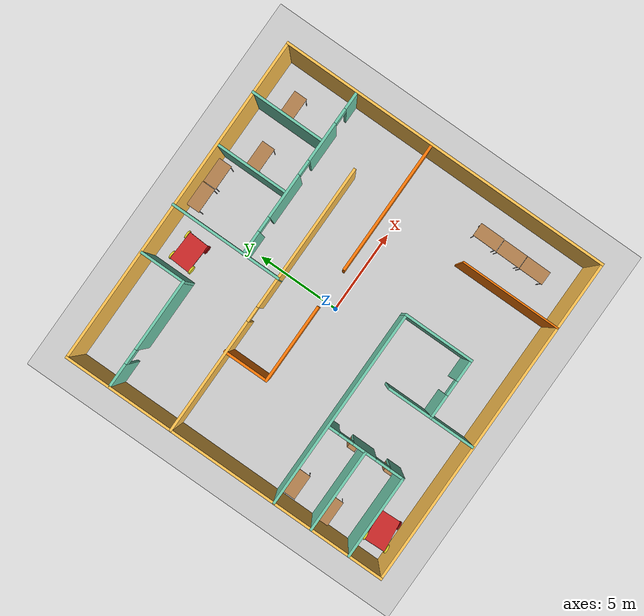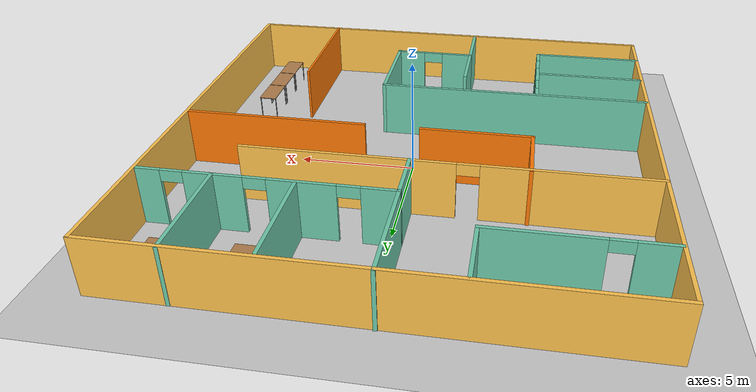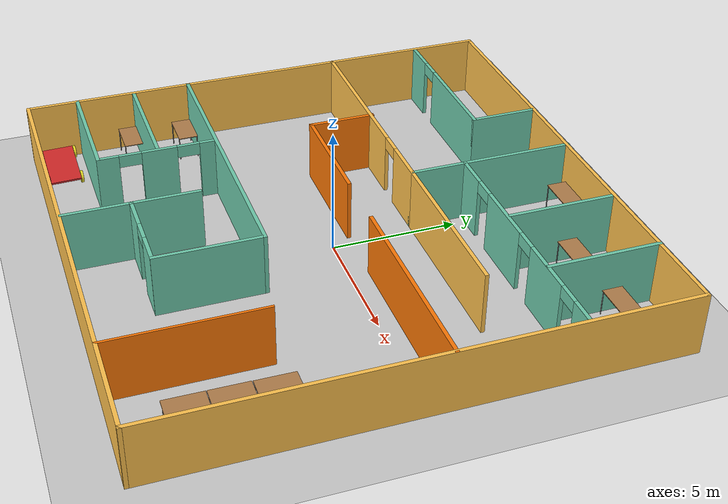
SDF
<sdf version="1.6">
 <world name="default">
  <light name="sun" type="directional">
   <pose>0 0 10 0 -0 0</pose>
   <diffuse>0.8 0.8 0.8 1</diffuse>
   <specular>0.2 0.2 0.2 1</specular>
   <attenuation>
    <range>1000</range>
    <constant>0.9</constant>
    <linear>0.01</linear>
    <quadratic>0.001</quadratic>
   </attenuation>
   <direction>-0.5 0.1 -0.9</direction>
  </light>
  <model name="ground_plane">
   <static>1</static>
   <link name="link">
    <collision name="collision">
     <geometry><plane><normal>0 0 1</normal><size>100 100</size></plane></geometry>
     <surface>
      <contact><collide_bitmask>65535</collide_bitmask></contact>
      <friction><ode><mu>100</mu><mu2>50</mu2></ode></friction>
     </surface>
    </collision>
    <visual name="visual">
     <cast_shadows>0</cast_shadows>
     <geometry><plane><normal>0 0 1</normal><size>100 100</size></plane></geometry>
     <material>
      <script><uri>file://media/materials/scripts/gazebo.material</uri><name>Gazebo/Grey</name></script>
     </material>
    </visual>
   </link>
  </model>
  <gravity>0 0 -9.8</gravity>
  <magnetic_field>6e-06 2.3e-05 -4.2e-05</magnetic_field>
  <atmosphere type="adiabatic"/>
  <physics name="default_physics" default="0" type="ode">
   <max_step_size>0.001</max_step_size>
   <real_time_factor>1</real_time_factor>
   <real_time_update_rate>1000</real_time_update_rate>
  </physics>
  <scene><ambient>0.4 0.4 0.4 1</ambient><background>0.7 0.7 0.7 1</background><shadows>1</shadows></scene>
  <audio><device>default</device></audio>
  <spherical_coordinates>
   <surface_model>EARTH_WGS84</surface_model>
   <latitude_deg>0</latitude_deg>
   <longitude_deg>0</longitude_deg>
   <elevation>0</elevation>
   <heading_deg>0</heading_deg>
  </spherical_coordinates>
  <model name="small_office">
   <pose>-0.11389 -0.002642 0 0 -0 0</pose>
   <link name="Wall_11">
    <collision name="Wall_11_Collision">
     <geometry><box><size>20 0.15 2.5</size></box></geometry>
     <pose>0 0 1.25 0 -0 0</pose>
    </collision>
    <visual name="Wall_11_Visual">
     <pose>0 0 1.25 0 -0 0</pose>
     <geometry><box><size>20 0.15 2.5</size></box></geometry>
     <material>
      <script><uri>file://media/materials/scripts/gazebo.material</uri><name>Gazebo/Grey</name></script>
      <ambient>1 0.764706 0.305882 1</ambient>
     </material>
     <meta><layer>0</layer></meta>
    </visual>
    <pose>9.925 -0.020313 0 0 -0 -1.5708</pose>
   </link>
   <link name="Wall_13">
    <collision name="Wall_13_Collision">
     <geometry><box><size>6 0.1 2.5</size></box></geometry>
     <pose>0 0 1.25 0 -0 0</pose>
    </collision>
    <visual name="Wall_13_Visual">
     <pose>0 0 1.25 0 -0 0</pose>
     <geometry><box><size>6 0.1 2.5</size></box></geometry>
     <material>
      <script><uri>file://media/materials/scripts/gazebo.material</uri><name>Gazebo/Grey</name></script>
      <ambient>0.996078 0.47451 0.0196078 1</ambient>
     </material>
     <meta><layer>0</layer></meta>
    </visual>
    <pose>5.89991 -6.99585 0 0 -0 -1.5708</pose>
   </link>
   <link name="Wall_15">
    <collision name="Wall_15_Collision">
     <geometry><box><size>4.25 0.15 2.5</size></box></geometry>
     <pose>0 0 1.25 0 -0 0</pose>
    </collision>
    <visual name="Wall_15_Visual">
     <pose>0 0 1.25 0 -0 0</pose>
     <geometry><box><size>4.25 0.15 2.5</size></box></geometry>
     <material>
      <script><uri>file://media/materials/scripts/gazebo.material</uri><name>Gazebo/Grey</name></script>
      <ambient>0.435294 0.796078 0.67451 1</ambient>
     </material>
     <meta><layer>0</layer></meta>
    </visual>
    <pose>1.96698 -5.229 0 0 -0 1.5708</pose>
   </link>
   <link name="Wall_17">
    <pose>0.146869 -7.279 0 0 -0 3.14159</pose>
    <visual name="Wall_17_Visual_0">
     <pose>-1.19969 0 1.25 0 -0 0</pose>
     <geometry><box><size>1.35062 0.15 2.5</size></box></geometry>
     <material>
      <script><uri>file://media/materials/scripts/gazebo.material</uri><name>Gazebo/Grey</name></script>
      <ambient>0.435294 0.796078 0.67451 1</ambient>
     </material>
     <meta><layer>0</layer></meta>
    </visual>
    <collision name="Wall_17_Collision_0">
     <geometry><box><size>1.35062 0.15 2.5</size></box></geometry>
     <pose>-1.19969 0 1.25 0 -0 0</pose>
    </collision>
    <visual name="Wall_17_Visual_1">
     <pose>1.12531 0 1.25 0 -0 0</pose>
     <geometry><box><size>1.49937 0.15 2.5</size></box></geometry>
     <material>
      <script><uri>file://media/materials/scripts/gazebo.material</uri><name>Gazebo/Grey</name></script>
      <ambient>0.435294 0.796078 0.67451 1</ambient>
     </material>
     <meta><layer>0</layer></meta>
    </visual>
    <collision name="Wall_17_Collision_1">
     <geometry><box><size>1.49937 0.15 2.5</size></box></geometry>
     <pose>1.12531 0 1.25 0 -0 0</pose>
    </collision>
    <visual name="Wall_17_Visual_2">
     <pose>-0.074375 0 2.25 0 -0 0</pose>
     <geometry><box><size>0.9 0.15 0.5</size></box></geometry>
     <material>
      <script><uri>file://media/materials/scripts/gazebo.material</uri><name>Gazebo/Grey</name></script>
      <ambient>0.435294 0.796078 0.67451 1</ambient>
     </material>
     <meta><layer>0</layer></meta>
    </visual>
    <collision name="Wall_17_Collision_2">
     <geometry><box><size>0.9 0.15 0.5</size></box></geometry>
     <pose>-0.074375 0 2.25 0 -0 0</pose>
    </collision>
   </link>
   <link name="Wall_25">
    <collision name="Wall_25_Collision">
     <geometry><box><size>2.75 0.15 2.5</size></box></geometry>
     <pose>0 0 1.25 0 -0 0</pose>
    </collision>
    <visual name="Wall_25_Visual">
     <pose>0 0 1.25 0 -0 0</pose>
     <geometry><box><size>2.75 0.15 2.5</size></box></geometry>
     <material>
      <script><uri>file://media/materials/scripts/gazebo.material</uri><name>Gazebo/Grey</name></script>
      <ambient>0.435294 0.796078 0.67451 1</ambient>
     </material>
     <meta><layer>0</layer></meta>
    </visual>
    <pose>-1.65313 -8.579 0 0 -0 -1.5708</pose>
   </link>
   <link name="Wall_28">
    <collision name="Wall_28_Collision">
     <geometry><box><size>2.75 0.15 2.5</size></box></geometry>
     <pose>0 0 1.25 0 -0 0</pose>
    </collision>
    <visual name="Wall_28_Visual">
     <pose>0 0 1.25 0 -0 0</pose>
     <geometry><box><size>2.75 0.15 2.5</size></box></geometry>
     <material>
      <script><uri>file://media/materials/scripts/gazebo.material</uri><name>Gazebo/Grey</name></script>
      <ambient>0.435294 0.796078 0.67451 1</ambient>
     </material>
     <meta><layer>0</layer></meta>
    </visual>
    <pose>-1.65313 -5.979 0 0 -0 -1.5708</pose>
   </link>
   <link name="Wall_32">
    <collision name="Wall_32_Collision">
     <geometry><box><size>5 0.15 2.5</size></box></geometry>
     <pose>0 0 1.25 0 -0 0</pose>
    </collision>
    <visual name="Wall_32_Visual">
     <pose>0 0 1.25 0 -0 0</pose>
     <geometry><box><size>5 0.15 2.5</size></box></geometry>
     <material>
      <script><uri>file://media/materials/scripts/gazebo.material</uri><name>Gazebo/Grey</name></script>
      <ambient>0.435294 0.796078 0.67451 1</ambient>
     </material>
     <meta><layer>0</layer></meta>
    </visual>
    <pose>-7.49031 -7.91366 0 0 -0 3.14159</pose>
   </link>
   <link name="Wall_34">
    <collision name="Wall_34_Collision">
     <geometry><box><size>5 0.15 2.5</size></box></geometry>
     <pose>0 0 1.25 0 -0 0</pose>
    </collision>
    <visual name="Wall_34_Visual">
     <pose>0 0 1.25 0 -0 0</pose>
     <geometry><box><size>5 0.15 2.5</size></box></geometry>
     <material>
      <script><uri>file://media/materials/scripts/gazebo.material</uri><name>Gazebo/Grey</name></script>
      <ambient>0.435294 0.796078 0.67451 1</ambient>
     </material>
     <meta><layer>0</layer></meta>
    </visual>
    <pose>-7.49358 -5.53605 0 0 -0 0</pose>
   </link>
   <link name="Wall_39">
    <collision name="Wall_39_Collision">
     <geometry><box><size>12 0.15 2.5</size></box></geometry>
     <pose>0 0 1.25 0 -0 0</pose>
    </collision>
    <visual name="Wall_39_Visual">
     <pose>0 0 1.25 0 -0 0</pose>
     <geometry><box><size>12 0.15 2.5</size></box></geometry>
     <material>
      <script><uri>file://media/materials/scripts/gazebo.material</uri><name>Gazebo/Grey</name></script>
      <ambient>0.435294 0.796078 0.67451 1</ambient>
     </material>
     <meta><layer>0</layer></meta>
    </visual>
    <pose>-3.95802 -3.179 0 0 -0 3.14159</pose>
   </link>
   <link name="Wall_41">
    <pose>-5.06531 -5.61366 0 0 -0 1.5708</pose>
    <visual name="Wall_41_Visual_0">
     <pose>-1.92932 0 1.25 0 -0 0</pose>
     <geometry><box><size>0.89135 0.15 2.5</size></box></geometry>
     <material>
      <script><uri>file://media/materials/scripts/gazebo.material</uri><name>Gazebo/Grey</name></script>
      <ambient>0.435294 0.796078 0.67451 1</ambient>
     </material>
     <meta><layer>0</layer></meta>
    </visual>
    <collision name="Wall_41_Collision_0">
     <geometry><box><size>0.89135 0.15 2.5</size></box></geometry>
     <pose>-1.92932 0 1.25 0 -0 0</pose>
    </collision>
    <visual name="Wall_41_Visual_1">
     <pose>0.13015 0 1.25 0 -0 0</pose>
     <geometry><box><size>1.4276 0.15 2.5</size></box></geometry>
     <material>
      <script><uri>file://media/materials/scripts/gazebo.material</uri><name>Gazebo/Grey</name></script>
      <ambient>0.435294 0.796078 0.67451 1</ambient>
     </material>
     <meta><layer>0</layer></meta>
    </visual>
    <collision name="Wall_41_Collision_1">
     <geometry><box><size>1.4276 0.15 2.5</size></box></geometry>
     <pose>0.13015 0 1.25 0 -0 0</pose>
    </collision>
    <visual name="Wall_41_Visual_2">
     <pose>2.05947 0 1.25 0 -0 0</pose>
     <geometry><box><size>0.63105 0.15 2.5</size></box></geometry>
     <material>
      <script><uri>file://media/materials/scripts/gazebo.material</uri><name>Gazebo/Grey</name></script>
      <ambient>0.435294 0.796078 0.67451 1</ambient>
     </material>
     <meta><layer>0</layer></meta>
    </visual>
    <collision name="Wall_41_Collision_2">
     <geometry><box><size>0.63105 0.15 2.5</size></box></geometry>
     <pose>2.05947 0 1.25 0 -0 0</pose>
    </collision>
    <visual name="Wall_41_Visual_3">
     <pose>-1.03365 0 2.25 0 -0 0</pose>
     <geometry><box><size>0.9 0.15 0.5</size></box></geometry>
     <material>
      <script><uri>file://media/materials/scripts/gazebo.material</uri><name>Gazebo/Grey</name></script>
      <ambient>0.435294 0.796078 0.67451 1</ambient>
     </material>
     <meta><layer>0</layer></meta>
    </visual>
    <collision name="Wall_41_Collision_3">
     <geometry><box><size>0.9 0.15 0.5</size></box></geometry>
     <pose>-1.03365 0 2.25 0 -0 0</pose>
    </collision>
    <visual name="Wall_41_Visual_4">
     <pose>1.29395 0 2.25 0 -0 0</pose>
     <geometry><box><size>0.9 0.15 0.5</size></box></geometry>
     <material>
      <script><uri>file://media/materials/scripts/gazebo.material</uri><name>Gazebo/Grey</name></script>
      <ambient>0.435294 0.796078 0.67451 1</ambient>
     </material>
     <meta><layer>0</layer></meta>
    </visual>
    <collision name="Wall_41_Collision_4">
     <geometry><box><size>0.9 0.15 0.5</size></box></geometry>
     <pose>1.29395 0 2.25 0 -0 0</pose>
    </collision>
   </link>
   <link name="Wall_43">
    <pose>-6.5641 7.23219 0 0 -0 0</pose>
    <visual name="Wall_43_Visual_0">
     <pose>-2.63259 0 1.25 0 -0 0</pose>
     <geometry><box><size>1.48482 0.15 2.5</size></box></geometry>
     <material>
      <script><uri>file://media/materials/scripts/gazebo.material</uri><name>Gazebo/Grey</name></script>
      <ambient>0.435294 0.796078 0.67451 1</ambient>
     </material>
     <meta><layer>0</layer></meta>
    </visual>
    <collision name="Wall_43_Collision_0">
     <geometry><box><size>1.48482 0.15 2.5</size></box></geometry>
     <pose>-2.63259 0 1.25 0 -0 0</pose>
    </collision>
    <visual name="Wall_43_Visual_1">
     <pose>1.19241 0 1.25 0 -0 0</pose>
     <geometry><box><size>4.36518 0.15 2.5</size></box></geometry>
     <material>
      <script><uri>file://media/materials/scripts/gazebo.material</uri><name>Gazebo/Grey</name></script>
      <ambient>0.435294 0.796078 0.67451 1</ambient>
     </material>
     <meta><layer>0</layer></meta>
    </visual>
    <collision name="Wall_43_Collision_1">
     <geometry><box><size>4.36518 0.15 2.5</size></box></geometry>
     <pose>1.19241 0 1.25 0 -0 0</pose>
    </collision>
    <visual name="Wall_43_Visual_2">
     <pose>-1.44018 0 2.25 0 -0 0</pose>
     <geometry><box><size>0.9 0.15 0.5</size></box></geometry>
     <material>
      <script><uri>file://media/materials/scripts/gazebo.material</uri><name>Gazebo/Grey</name></script>
      <ambient>0.435294 0.796078 0.67451 1</ambient>
     </material>
     <meta><layer>0</layer></meta>
    </visual>
    <collision name="Wall_43_Collision_2">
     <geometry><box><size>0.9 0.15 0.5</size></box></geometry>
     <pose>-1.44018 0 2.25 0 -0 0</pose>
    </collision>
   </link>
   <link name="Wall_44">
    <collision name="Wall_44_Collision">
     <geometry><box><size>2.75 0.15 2.5</size></box></geometry>
     <pose>0 0 1.25 0 -0 0</pose>
    </collision>
    <visual name="Wall_44_Visual">
     <pose>0 0 1.25 0 -0 0</pose>
     <geometry><box><size>2.75 0.15 2.5</size></box></geometry>
     <material>
      <script><uri>file://media/materials/scripts/gazebo.material</uri><name>Gazebo/Grey</name></script>
      <ambient>0.435294 0.796078 0.67451 1</ambient>
     </material>
     <meta><layer>0</layer></meta>
    </visual>
    <pose>-3.2641 8.53219 0 0 -0 1.5708</pose>
   </link>
   <link name="Wall_47">
    <pose>-5.108 3.34531 0 0 -0 0</pose>
    <visual name="Wall_47_Visual_0">
     <pose>-1.40255 0 1.25 0 -0 0</pose>
     <geometry><box><size>6.9449 0.15 2.5</size></box></geometry>
     <material>
      <script><uri>file://media/materials/scripts/gazebo.material</uri><name>Gazebo/Grey</name></script>
      <ambient>1 0.764706 0.305882 1</ambient>
     </material>
     <meta><layer>0</layer></meta>
    </visual>
    <collision name="Wall_47_Collision_0">
     <geometry><box><size>6.9449 0.15 2.5</size></box></geometry>
     <pose>-1.40255 0 1.25 0 -0 0</pose>
    </collision>
    <visual name="Wall_47_Visual_1">
     <pose>3.92245 0 1.25 0 -0 0</pose>
     <geometry><box><size>1.9051 0.15 2.5</size></box></geometry>
     <material>
      <script><uri>file://media/materials/scripts/gazebo.material</uri><name>Gazebo/Grey</name></script>
      <ambient>1 0.764706 0.305882 1</ambient>
     </material>
     <meta><layer>0</layer></meta>
    </visual>
    <collision name="Wall_47_Collision_1">
     <geometry><box><size>1.9051 0.15 2.5</size></box></geometry>
     <pose>3.92245 0 1.25 0 -0 0</pose>
    </collision>
    <visual name="Wall_47_Visual_2">
     <pose>2.5199 0 2.25 0 -0 0</pose>
     <geometry><box><size>0.9 0.15 0.5</size></box></geometry>
     <material>
      <script><uri>file://media/materials/scripts/gazebo.material</uri><name>Gazebo/Grey</name></script>
      <ambient>1 0.764706 0.305882 1</ambient>
     </material>
     <meta><layer>0</layer></meta>
    </visual>
    <collision name="Wall_47_Collision_2">
     <geometry><box><size>0.9 0.15 0.5</size></box></geometry>
     <pose>2.5199 0 2.25 0 -0 0</pose>
    </collision>
   </link>
   <link name="Wall_48">
    <collision name="Wall_48_Collision">
     <geometry><box><size>6.75 0.15 2.5</size></box></geometry>
     <pose>0 0 1.25 0 -0 0</pose>
    </collision>
    <visual name="Wall_48_Visual">
     <pose>0 0 1.25 0 -0 0</pose>
     <geometry><box><size>6.75 0.15 2.5</size></box></geometry>
     <material>
      <script><uri>file://media/materials/scripts/gazebo.material</uri><name>Gazebo/Grey</name></script>
      <ambient>0.435294 0.796078 0.67451 1</ambient>
     </material>
     <meta><layer>0</layer></meta>
    </visual>
    <pose>-0.307996 6.64531 0 0 -0 1.5708</pose>
   </link>
   <link name="Wall_5">
    <collision name="Wall_5_Collision">
     <geometry><box><size>20 0.15 2.5</size></box></geometry>
     <pose>0 0 1.25 0 -0 0</pose>
    </collision>
    <visual name="Wall_5_Visual">
     <pose>0 0 1.25 0 -0 0</pose>
     <geometry><box><size>20 0.15 2.5</size></box></geometry>
     <material>
      <script><uri>file://media/materials/scripts/gazebo.material</uri><name>Gazebo/Grey</name></script>
      <ambient>1 0.764706 0.305882 1</ambient>
     </material>
     <meta><layer>0</layer></meta>
    </visual>
    <pose>-9.925 -0.020313 0 0 -0 -1.5708</pose>
   </link>
   <link name="Wall_51">
    <collision name="Wall_51_Collision">
     <geometry><box><size>4.75 0.15 2.5</size></box></geometry>
     <pose>0 0 1.25 0 -0 0</pose>
    </collision>
    <visual name="Wall_51_Visual">
     <pose>0 0 1.25 0 -0 0</pose>
     <geometry><box><size>4.75 0.15 2.5</size></box></geometry>
     <material>
      <script><uri>file://media/materials/scripts/gazebo.material</uri><name>Gazebo/Grey</name></script>
      <ambient>0.996078 0.47451 0.0196078 1</ambient>
     </material>
     <meta><layer>0</layer></meta>
    </visual>
    <pose>-2.67646 0.791838 0 0 -0 0</pose>
   </link>
   <link name="Wall_53">
    <collision name="Wall_53_Collision">
     <geometry><box><size>8 0.15 2.5</size></box></geometry>
     <pose>0 0 1.25 0 -0 0</pose>
    </collision>
    <visual name="Wall_53_Visual">
     <pose>0 0 1.25 0 -0 0</pose>
     <geometry><box><size>8 0.15 2.5</size></box></geometry>
     <material>
      <script><uri>file://media/materials/scripts/gazebo.material</uri><name>Gazebo/Grey</name></script>
      <ambient>0.996078 0.47451 0.0196078 1</ambient>
     </material>
     <meta><layer>0</layer></meta>
    </visual>
    <pose>5.99489 0.810335 0 0 -0 0</pose>
   </link>
   <link name="Wall_60">
    <collision name="Wall_60_Collision">
     <geometry><box><size>2.75 0.15 2.5</size></box></geometry>
     <pose>0 0 1.25 0 -0 0</pose>
    </collision>
    <visual name="Wall_60_Visual">
     <pose>0 0 1.25 0 -0 0</pose>
     <geometry><box><size>2.75 0.15 2.5</size></box></geometry>
     <material>
      <script><uri>file://media/materials/scripts/gazebo.material</uri><name>Gazebo/Grey</name></script>
      <ambient>0.996078 0.47451 0.0196078 1</ambient>
     </material>
     <meta><layer>0</layer></meta>
    </visual>
    <pose>-4.97646 2.09184 0 0 -0 1.5708</pose>
   </link>
   <link name="Wall_65">
    <pose>4.73757 5.53645 0 0 -0 0</pose>
    <visual name="Wall_65_Visual_0">
     <pose>-4.3785 0 1.25 0 -0 0</pose>
     <geometry><box><size>1.493 0.15 2.5</size></box></geometry>
     <material>
      <script><uri>file://media/materials/scripts/gazebo.material</uri><name>Gazebo/Grey</name></script>
      <ambient>0.435294 0.796078 0.67451 1</ambient>
     </material>
     <meta><layer>0</layer></meta>
    </visual>
    <collision name="Wall_65_Collision_0">
     <geometry><box><size>1.493 0.15 2.5</size></box></geometry>
     <pose>-4.3785 0 1.25 0 -0 0</pose>
    </collision>
    <visual name="Wall_65_Visual_1">
     <pose>-1.38981 0 1.25 0 -0 0</pose>
     <geometry><box><size>2.68438 0.15 2.5</size></box></geometry>
     <material>
      <script><uri>file://media/materials/scripts/gazebo.material</uri><name>Gazebo/Grey</name></script>
      <ambient>0.435294 0.796078 0.67451 1</ambient>
     </material>
     <meta><layer>0</layer></meta>
    </visual>
    <collision name="Wall_65_Collision_1">
     <geometry><box><size>2.68438 0.15 2.5</size></box></geometry>
     <pose>-1.38981 0 1.25 0 -0 0</pose>
    </collision>
    <visual name="Wall_65_Visual_2">
     <pose>2.03308 0 1.25 0 -0 0</pose>
     <geometry><box><size>2.36142 0.15 2.5</size></box></geometry>
     <material>
      <script><uri>file://media/materials/scripts/gazebo.material</uri><name>Gazebo/Grey</name></script>
      <ambient>0.435294 0.796078 0.67451 1</ambient>
     </material>
     <meta><layer>0</layer></meta>
    </visual>
    <collision name="Wall_65_Collision_2">
     <geometry><box><size>2.36142 0.15 2.5</size></box></geometry>
     <pose>2.03308 0 1.25 0 -0 0</pose>
    </collision>
    <visual name="Wall_65_Visual_3">
     <pose>4.61939 0 1.25 0 -0 0</pose>
     <geometry><box><size>1.01121 0.15 2.5</size></box></geometry>
     <material>
      <script><uri>file://media/materials/scripts/gazebo.material</uri><name>Gazebo/Grey</name></script>
      <ambient>0.435294 0.796078 0.67451 1</ambient>
     </material>
     <meta><layer>0</layer></meta>
    </visual>
    <collision name="Wall_65_Collision_3">
     <geometry><box><size>1.01121 0.15 2.5</size></box></geometry>
     <pose>4.61939 0 1.25 0 -0 0</pose>
    </collision>
    <visual name="Wall_65_Visual_4">
     <pose>-3.182 0 2.25 0 -0 0</pose>
     <geometry><box><size>0.9 0.15 0.5</size></box></geometry>
     <material>
      <script><uri>file://media/materials/scripts/gazebo.material</uri><name>Gazebo/Grey</name></script>
      <ambient>0.435294 0.796078 0.67451 1</ambient>
     </material>
     <meta><layer>0</layer></meta>
    </visual>
    <collision name="Wall_65_Collision_4">
     <geometry><box><size>0.9 0.15 0.5</size></box></geometry>
     <pose>-3.182 0 2.25 0 -0 0</pose>
    </collision>
    <visual name="Wall_65_Visual_5">
     <pose>0.402374 0 2.25 0 -0 0</pose>
     <geometry><box><size>0.9 0.15 0.5</size></box></geometry>
     <material>
      <script><uri>file://media/materials/scripts/gazebo.material</uri><name>Gazebo/Grey</name></script>
      <ambient>0.435294 0.796078 0.67451 1</ambient>
     </material>
     <meta><layer>0</layer></meta>
    </visual>
    <collision name="Wall_65_Collision_5">
     <geometry><box><size>0.9 0.15 0.5</size></box></geometry>
     <pose>0.402374 0 2.25 0 -0 0</pose>
    </collision>
    <visual name="Wall_65_Visual_6">
     <pose>3.66379 0 2.25 0 -0 0</pose>
     <geometry><box><size>0.9 0.15 0.5</size></box></geometry>
     <material>
      <script><uri>file://media/materials/scripts/gazebo.material</uri><name>Gazebo/Grey</name></script>
      <ambient>0.435294 0.796078 0.67451 1</ambient>
     </material>
     <meta><layer>0</layer></meta>
    </visual>
    <collision name="Wall_65_Collision_6">
     <geometry><box><size>0.9 0.15 0.5</size></box></geometry>
     <pose>3.66379 0 2.25 0 -0 0</pose>
    </collision>
   </link>
   <link name="Wall_67">
    <collision name="Wall_67_Collision">
     <geometry><box><size>7 0.15 2.5</size></box></geometry>
     <pose>0 0 1.25 0 -0 0</pose>
    </collision>
    <visual name="Wall_67_Visual">
     <pose>0 0 1.25 0 -0 0</pose>
     <geometry><box><size>7 0.15 2.5</size></box></geometry>
     <material>
      <script><uri>file://media/materials/scripts/gazebo.material</uri><name>Gazebo/Grey</name></script>
      <ambient>1 0.764706 0.305882 1</ambient>
     </material>
     <meta><layer>0</layer></meta>
    </visual>
    <pose>3.117 3.34531 0 0 -0 0</pose>
   </link>
   <link name="Wall_69">
    <collision name="Wall_69_Collision">
     <geometry><box><size>4.25 0.15 2.5</size></box></geometry>
     <pose>0 0 1.25 0 -0 0</pose>
    </collision>
    <visual name="Wall_69_Visual">
     <pose>0 0 1.25 0 -0 0</pose>
     <geometry><box><size>4.25 0.15 2.5</size></box></geometry>
     <material>
      <script><uri>file://media/materials/scripts/gazebo.material</uri><name>Gazebo/Grey</name></script>
      <ambient>0.435294 0.796078 0.67451 1</ambient>
     </material>
     <meta><layer>0</layer></meta>
    </visual>
    <pose>3.55687 7.70224 0 0 -0 1.5708</pose>
   </link>
   <link name="Wall_7">
    <collision name="Wall_7_Collision">
     <geometry><box><size>20 0.15 2.5</size></box></geometry>
     <pose>0 0 1.25 0 -0 0</pose>
    </collision>
    <visual name="Wall_7_Visual">
     <pose>0 0 1.25 0 -0 0</pose>
     <geometry><box><size>20 0.15 2.5</size></box></geometry>
     <material>
      <script><uri>file://media/materials/scripts/gazebo.material</uri><name>Gazebo/Grey</name></script>
      <ambient>1 0.764706 0.305882 1</ambient>
     </material>
     <meta><layer>0</layer></meta>
    </visual>
    <pose>-0 -9.94531 0 0 -0 0</pose>
   </link>
   <link name="Wall_73">
    <collision name="Wall_73_Collision">
     <geometry><box><size>4.5 0.15 2.5</size></box></geometry>
     <pose>0 0 1.25 0 -0 0</pose>
    </collision>
    <visual name="Wall_73_Visual">
     <pose>0 0 1.25 0 -0 0</pose>
     <geometry><box><size>4.5 0.15 2.5</size></box></geometry>
     <material>
      <script><uri>file://media/materials/scripts/gazebo.material</uri><name>Gazebo/Grey</name></script>
      <ambient>0.435294 0.796078 0.67451 1</ambient>
     </material>
     <meta><layer>0</layer></meta>
    </visual>
    <pose>6.81213 7.74342 0 0 -0 1.5708</pose>
   </link>
   <link name="Wall_9">
    <collision name="Wall_9_Collision">
     <geometry><box><size>20 0.15 2.5</size></box></geometry>
     <pose>0 0 1.25 0 -0 0</pose>
    </collision>
    <visual name="Wall_9_Visual">
     <pose>0 0 1.25 0 -0 0</pose>
     <geometry><box><size>20 0.15 2.5</size></box></geometry>
     <material>
      <script><uri>file://media/materials/scripts/gazebo.material</uri><name>Gazebo/Grey</name></script>
      <ambient>1 0.764706 0.305882 1</ambient>
     </material>
     <meta><layer>0</layer></meta>
    </visual>
    <pose>-0 9.90469 0 0 -0 0</pose>
   </link>
   <static>1</static>
  </model>
  <model name="table">
   <static>1</static>
   <link name="link">
    <collision name="surface">
     <pose>0 0 1 0 -0 0</pose>
     <geometry><box><size>1.5 0.8 0.03</size></box></geometry>
     <surface><friction><ode><mu>0.6</mu><mu2>0.6</mu2></ode></friction></surface>
    </collision>
    <visual name="visual1">
     <pose>0 0 1 0 -0 0</pose>
     <geometry><box><size>1.5 0.8 0.03</size></box></geometry>
     <material>
      <script><uri>file://media/materials/scripts/gazebo.material</uri><name>Gazebo/Wood</name></script>
     </material>
    </visual>
    <collision name="front_left_leg">
     <pose>0.68 0.38 0.5 0 -0 0</pose>
     <geometry><cylinder><radius>0.02</radius><length>1</length></cylinder></geometry>
    </collision>
    <visual name="front_left_leg">
     <pose>0.68 0.38 0.5 0 -0 0</pose>
     <geometry><cylinder><radius>0.02</radius><length>1</length></cylinder></geometry>
     <material>
      <script><uri>file://media/materials/scripts/gazebo.material</uri><name>Gazebo/Grey</name></script>
     </material>
    </visual>
    <collision name="front_right_leg">
     <pose>0.68 -0.38 0.5 0 -0 0</pose>
     <geometry><cylinder><radius>0.02</radius><length>1</length></cylinder></geometry>
    </collision>
    <visual name="front_right_leg">
     <pose>0.68 -0.38 0.5 0 -0 0</pose>
     <geometry><cylinder><radius>0.02</radius><length>1</length></cylinder></geometry>
     <material>
      <script><uri>file://media/materials/scripts/gazebo.material</uri><name>Gazebo/Grey</name></script>
     </material>
    </visual>
    <collision name="back_right_leg">
     <pose>-0.68 -0.38 0.5 0 -0 0</pose>
     <geometry><cylinder><radius>0.02</radius><length>1</length></cylinder></geometry>
    </collision>
    <visual name="back_right_leg">
     <pose>-0.68 -0.38 0.5 0 -0 0</pose>
     <geometry><cylinder><radius>0.02</radius><length>1</length></cylinder></geometry>
     <material>
      <script><uri>file://media/materials/scripts/gazebo.material</uri><name>Gazebo/Grey</name></script>
     </material>
    </visual>
    <collision name="back_left_leg">
     <pose>-0.68 0.38 0.5 0 -0 0</pose>
     <geometry><cylinder><radius>0.02</radius><length>1</length></cylinder></geometry>
    </collision>
    <visual name="back_left_leg">
     <pose>-0.68 0.38 0.5 0 -0 0</pose>
     <geometry><cylinder><radius>0.02</radius><length>1</length></cylinder></geometry>
     <material>
      <script><uri>file://media/materials/scripts/gazebo.material</uri><name>Gazebo/Grey</name></script>
     </material>
    </visual>
   </link>
   <pose>-8.89453 -3.69923 0 0 -0 0</pose>
  </model>
  <model name="table_0">
   <static>1</static>
   <link name="link">
    <collision name="surface">
     <pose>0 0 1 0 -0 0</pose>
     <geometry><box><size>1.5 0.8 0.03</size></box></geometry>
     <surface><friction><ode><mu>0.6</mu><mu2>0.6</mu2></ode></friction></surface>
    </collision>
    <visual name="visual1">
     <pose>0 0 1 0 -0 0</pose>
     <geometry><box><size>1.5 0.8 0.03</size></box></geometry>
     <material>
      <script><uri>file://media/materials/scripts/gazebo.material</uri><name>Gazebo/Wood</name></script>
     </material>
    </visual>
    <collision name="front_left_leg">
     <pose>0.68 0.38 0.5 0 -0 0</pose>
     <geometry><cylinder><radius>0.02</radius><length>1</length></cylinder></geometry>
    </collision>
    <visual name="front_left_leg">
     <pose>0.68 0.38 0.5 0 -0 0</pose>
     <geometry><cylinder><radius>0.02</radius><length>1</length></cylinder></geometry>
     <material>
      <script><uri>file://media/materials/scripts/gazebo.material</uri><name>Gazebo/Grey</name></script>
     </material>
    </visual>
    <collision name="front_right_leg">
     <pose>0.68 -0.38 0.5 0 -0 0</pose>
     <geometry><cylinder><radius>0.02</radius><length>1</length></cylinder></geometry>
    </collision>
    <visual name="front_right_leg">
     <pose>0.68 -0.38 0.5 0 -0 0</pose>
     <geometry><cylinder><radius>0.02</radius><length>1</length></cylinder></geometry>
     <material>
      <script><uri>file://media/materials/scripts/gazebo.material</uri><name>Gazebo/Grey</name></script>
     </material>
    </visual>
    <collision name="back_right_leg">
     <pose>-0.68 -0.38 0.5 0 -0 0</pose>
     <geometry><cylinder><radius>0.02</radius><length>1</length></cylinder></geometry>
    </collision>
    <visual name="back_right_leg">
     <pose>-0.68 -0.38 0.5 0 -0 0</pose>
     <geometry><cylinder><radius>0.02</radius><length>1</length></cylinder></geometry>
     <material>
      <script><uri>file://media/materials/scripts/gazebo.material</uri><name>Gazebo/Grey</name></script>
     </material>
    </visual>
    <collision name="back_left_leg">
     <pose>-0.68 0.38 0.5 0 -0 0</pose>
     <geometry><cylinder><radius>0.02</radius><length>1</length></cylinder></geometry>
    </collision>
    <visual name="back_left_leg">
     <pose>-0.68 0.38 0.5 0 -0 0</pose>
     <geometry><cylinder><radius>0.02</radius><length>1</length></cylinder></geometry>
     <material>
      <script><uri>file://media/materials/scripts/gazebo.material</uri><name>Gazebo/Grey</name></script>
     </material>
    </visual>
   </link>
   <pose>-9.03842 -5.96629 0 0 -0 0</pose>
  </model>
  <model name="cabinet">
   <static>1</static>
   <link name="cabinet_bottom_plate">
    <inertial>
     <pose>0 0 -1 0 -0 0</pose>
     <inertia><ixx>2.05</ixx><ixy>0</ixy><ixz>0</ixz><iyy>2.05</iyy><iyz>0</iyz><izz>2.05</izz></inertia>
     <mass>25</mass>
    </inertial>
    <collision name="cabinet_bottom_plate_geom">
     <pose>0 0 0.01 0 -0 0</pose>
     <geometry><box><size>0.45 0.45 0.02</size></box></geometry>
    </collision>
    <visual name="cabinet_bottom_plate_geom_visual">
     <pose>0 0 0.01 0 -0 0</pose>
     <geometry><box><size>0.45 0.45 0.02</size></box></geometry>
     <material>
      <script><uri>file://media/materials/scripts/gazebo.material</uri><name>Gazebo/Wood</name></script>
     </material>
    </visual>
    <collision name="cabinet_bottom_plate_geom_cabinet_back_plate">
     <pose>0.235 0 0.51 0 -0 0</pose>
     <geometry><box><size>0.02 0.45 1.02</size></box></geometry>
    </collision>
    <visual name="cabinet_bottom_plate_geom_cabinet_back_plate_visual">
     <pose>0.235 0 0.51 0 -0 0</pose>
     <geometry><box><size>0.02 0.45 1.02</size></box></geometry>
     <material>
      <script><uri>file://media/materials/scripts/gazebo.material</uri><name>Gazebo/Wood</name></script>
     </material>
    </visual>
    <collision name="cabinet_bottom_plate_geom_cabinet_left_plate">
     <pose>0 0.235 0.51 0 -0 0</pose>
     <geometry><box><size>0.45 0.02 1.02</size></box></geometry>
    </collision>
    <visual name="cabinet_bottom_plate_geom_cabinet_left_plate_visual">
     <pose>0 0.235 0.51 0 -0 0</pose>
     <geometry><box><size>0.45 0.02 1.02</size></box></geometry>
     <material>
      <script><uri>file://media/materials/scripts/gazebo.material</uri><name>Gazebo/Wood</name></script>
     </material>
    </visual>
    <collision name="cabinet_bottom_plate_geom_cabinet_middle_plate">
     <pose>0 0 0.51 0 -0 0</pose>
     <geometry><box><size>0.45 0.45 0.02</size></box></geometry>
    </collision>
    <visual name="cabinet_bottom_plate_geom_cabinet_middle_plate_visual">
     <pose>0 0 0.51 0 -0 0</pose>
     <geometry><box><size>0.45 0.45 0.02</size></box></geometry>
     <material>
      <script><uri>file://media/materials/scripts/gazebo.material</uri><name>Gazebo/Wood</name></script>
     </material>
    </visual>
    <collision name="cabinet_bottom_plate_geom_cabinet_right_plate">
     <pose>0 -0.235 0.51 0 -0 0</pose>
     <geometry><box><size>0.45 0.02 1.02</size></box></geometry>
    </collision>
    <visual name="cabinet_bottom_plate_geom_cabinet_right_plate_visual">
     <pose>0 -0.235 0.51 0 -0 0</pose>
     <geometry><box><size>0.45 0.02 1.02</size></box></geometry>
     <material>
      <script><uri>file://media/materials/scripts/gazebo.material</uri><name>Gazebo/Wood</name></script>
     </material>
    </visual>
    <collision name="cabinet_bottom_plate_geom_cabinet_top_plate">
     <pose>0 0 1.01 0 -0 0</pose>
     <geometry><box><size>0.45 0.45 0.02</size></box></geometry>
    </collision>
    <visual name="cabinet_bottom_plate_geom_cabinet_top_plate_visual">
     <pose>0 0 1.01 0 -0 0</pose>
     <geometry><box><size>0.45 0.45 0.02</size></box></geometry>
     <material>
      <script><uri>file://media/materials/scripts/gazebo.material</uri><name>Gazebo/Wood</name></script>
     </material>
    </visual>
   </link>
   <pose>-5.48498 -5.024 0 0 -0 0</pose>
  </model>
  <model name="cabinet_0">
   <static>1</static>
   <link name="cabinet_bottom_plate">
    <inertial>
     <pose>0 0 -1 0 -0 0</pose>
     <inertia><ixx>2.05</ixx><ixy>0</ixy><ixz>0</ixz><iyy>2.05</iyy><iyz>0</iyz><izz>2.05</izz></inertia>
     <mass>25</mass>
    </inertial>
    <collision name="cabinet_bottom_plate_geom">
     <pose>0 0 0.01 0 -0 0</pose>
     <geometry><box><size>0.45 0.45 0.02</size></box></geometry>
    </collision>
    <visual name="cabinet_bottom_plate_geom_visual">
     <pose>0 0 0.01 0 -0 0</pose>
     <geometry><box><size>0.45 0.45 0.02</size></box></geometry>
     <material>
      <script><uri>file://media/materials/scripts/gazebo.material</uri><name>Gazebo/Wood</name></script>
     </material>
    </visual>
    <collision name="cabinet_bottom_plate_geom_cabinet_back_plate">
     <pose>0.235 0 0.51 0 -0 0</pose>
     <geometry><box><size>0.02 0.45 1.02</size></box></geometry>
    </collision>
    <visual name="cabinet_bottom_plate_geom_cabinet_back_plate_visual">
     <pose>0.235 0 0.51 0 -0 0</pose>
     <geometry><box><size>0.02 0.45 1.02</size></box></geometry>
     <material>
      <script><uri>file://media/materials/scripts/gazebo.material</uri><name>Gazebo/Wood</name></script>
     </material>
    </visual>
    <collision name="cabinet_bottom_plate_geom_cabinet_left_plate">
     <pose>0 0.235 0.51 0 -0 0</pose>
     <geometry><box><size>0.45 0.02 1.02</size></box></geometry>
    </collision>
    <visual name="cabinet_bottom_plate_geom_cabinet_left_plate_visual">
     <pose>0 0.235 0.51 0 -0 0</pose>
     <geometry><box><size>0.45 0.02 1.02</size></box></geometry>
     <material>
      <script><uri>file://media/materials/scripts/gazebo.material</uri><name>Gazebo/Wood</name></script>
     </material>
    </visual>
    <collision name="cabinet_bottom_plate_geom_cabinet_middle_plate">
     <pose>0 0 0.51 0 -0 0</pose>
     <geometry><box><size>0.45 0.45 0.02</size></box></geometry>
    </collision>
    <visual name="cabinet_bottom_plate_geom_cabinet_middle_plate_visual">
     <pose>0 0 0.51 0 -0 0</pose>
     <geometry><box><size>0.45 0.45 0.02</size></box></geometry>
     <material>
      <script><uri>file://media/materials/scripts/gazebo.material</uri><name>Gazebo/Wood</name></script>
     </material>
    </visual>
    <collision name="cabinet_bottom_plate_geom_cabinet_right_plate">
     <pose>0 -0.235 0.51 0 -0 0</pose>
     <geometry><box><size>0.45 0.02 1.02</size></box></geometry>
    </collision>
    <visual name="cabinet_bottom_plate_geom_cabinet_right_plate_visual">
     <pose>0 -0.235 0.51 0 -0 0</pose>
     <geometry><box><size>0.45 0.02 1.02</size></box></geometry>
     <material>
      <script><uri>file://media/materials/scripts/gazebo.material</uri><name>Gazebo/Wood</name></script>
     </material>
    </visual>
    <collision name="cabinet_bottom_plate_geom_cabinet_top_plate">
     <pose>0 0 1.01 0 -0 0</pose>
     <geometry><box><size>0.45 0.45 0.02</size></box></geometry>
    </collision>
    <visual name="cabinet_bottom_plate_geom_cabinet_top_plate_visual">
     <pose>0 0 1.01 0 -0 0</pose>
     <geometry><box><size>0.45 0.45 0.02</size></box></geometry>
     <material>
      <script><uri>file://media/materials/scripts/gazebo.material</uri><name>Gazebo/Wood</name></script>
     </material>
    </visual>
   </link>
   <pose>-5.41384 -7.35141 0 0 -0 0</pose>
  </model>
  <model name="table_1">
   <static>1</static>
   <link name="link">
    <collision name="surface">
     <pose>0 0 1 0 -0 0</pose>
     <geometry><box><size>1.5 0.8 0.03</size></box></geometry>
     <surface><friction><ode><mu>0.6</mu><mu2>0.6</mu2></ode></friction></surface>
    </collision>
    <visual name="visual1">
     <pose>0 0 1 0 -0 0</pose>
     <geometry><box><size>1.5 0.8 0.03</size></box></geometry>
     <material>
      <script><uri>file://media/materials/scripts/gazebo.material</uri><name>Gazebo/Wood</name></script>
     </material>
    </visual>
    <collision name="front_left_leg">
     <pose>0.68 0.38 0.5 0 -0 0</pose>
     <geometry><cylinder><radius>0.02</radius><length>1</length></cylinder></geometry>
    </collision>
    <visual name="front_left_leg">
     <pose>0.68 0.38 0.5 0 -0 0</pose>
     <geometry><cylinder><radius>0.02</radius><length>1</length></cylinder></geometry>
     <material>
      <script><uri>file://media/materials/scripts/gazebo.material</uri><name>Gazebo/Grey</name></script>
     </material>
    </visual>
    <collision name="front_right_leg">
     <pose>0.68 -0.38 0.5 0 -0 0</pose>
     <geometry><cylinder><radius>0.02</radius><length>1</length></cylinder></geometry>
    </collision>
    <visual name="front_right_leg">
     <pose>0.68 -0.38 0.5 0 -0 0</pose>
     <geometry><cylinder><radius>0.02</radius><length>1</length></cylinder></geometry>
     <material>
      <script><uri>file://media/materials/scripts/gazebo.material</uri><name>Gazebo/Grey</name></script>
     </material>
    </visual>
    <collision name="back_right_leg">
     <pose>-0.68 -0.38 0.5 0 -0 0</pose>
     <geometry><cylinder><radius>0.02</radius><length>1</length></cylinder></geometry>
    </collision>
    <visual name="back_right_leg">
     <pose>-0.68 -0.38 0.5 0 -0 0</pose>
     <geometry><cylinder><radius>0.02</radius><length>1</length></cylinder></geometry>
     <material>
      <script><uri>file://media/materials/scripts/gazebo.material</uri><name>Gazebo/Grey</name></script>
     </material>
    </visual>
    <collision name="back_left_leg">
     <pose>-0.68 0.38 0.5 0 -0 0</pose>
     <geometry><cylinder><radius>0.02</radius><length>1</length></cylinder></geometry>
    </collision>
    <visual name="back_left_leg">
     <pose>-0.68 0.38 0.5 0 -0 0</pose>
     <geometry><cylinder><radius>0.02</radius><length>1</length></cylinder></geometry>
     <material>
      <script><uri>file://media/materials/scripts/gazebo.material</uri><name>Gazebo/Grey</name></script>
     </material>
    </visual>
   </link>
   <pose>7.89959 -4.52252 0 0 0 -1.57913</pose>
  </model>
  <model name="table_1_clone">
   <static>1</static>
   <link name="link">
    <collision name="surface">
     <pose>0 0 1 0 -0 0</pose>
     <geometry><box><size>1.5 0.8 0.03</size></box></geometry>
     <surface><friction><ode><mu>0.6</mu><mu2>0.6</mu2></ode></friction></surface>
    </collision>
    <visual name="visual1">
     <pose>0 0 1 0 -0 0</pose>
     <geometry><box><size>1.5 0.8 0.03</size></box></geometry>
     <material>
      <script><uri>file://media/materials/scripts/gazebo.material</uri><name>Gazebo/Wood</name></script>
     </material>
    </visual>
    <collision name="front_left_leg">
     <pose>0.68 0.38 0.5 0 -0 0</pose>
     <geometry><cylinder><radius>0.02</radius><length>1</length></cylinder></geometry>
    </collision>
    <visual name="front_left_leg">
     <pose>0.68 0.38 0.5 0 -0 0</pose>
     <geometry><cylinder><radius>0.02</radius><length>1</length></cylinder></geometry>
     <material>
      <script><uri>file://media/materials/scripts/gazebo.material</uri><name>Gazebo/Grey</name></script>
     </material>
    </visual>
    <collision name="front_right_leg">
     <pose>0.68 -0.38 0.5 0 -0 0</pose>
     <geometry><cylinder><radius>0.02</radius><length>1</length></cylinder></geometry>
    </collision>
    <visual name="front_right_leg">
     <pose>0.68 -0.38 0.5 0 -0 0</pose>
     <geometry><cylinder><radius>0.02</radius><length>1</length></cylinder></geometry>
     <material>
      <script><uri>file://media/materials/scripts/gazebo.material</uri><name>Gazebo/Grey</name></script>
     </material>
    </visual>
    <collision name="back_right_leg">
     <pose>-0.68 -0.38 0.5 0 -0 0</pose>
     <geometry><cylinder><radius>0.02</radius><length>1</length></cylinder></geometry>
    </collision>
    <visual name="back_right_leg">
     <pose>-0.68 -0.38 0.5 0 -0 0</pose>
     <geometry><cylinder><radius>0.02</radius><length>1</length></cylinder></geometry>
     <material>
      <script><uri>file://media/materials/scripts/gazebo.material</uri><name>Gazebo/Grey</name></script>
     </material>
    </visual>
    <collision name="back_left_leg">
     <pose>-0.68 0.38 0.5 0 -0 0</pose>
     <geometry><cylinder><radius>0.02</radius><length>1</length></cylinder></geometry>
    </collision>
    <visual name="back_left_leg">
     <pose>-0.68 0.38 0.5 0 -0 0</pose>
     <geometry><cylinder><radius>0.02</radius><length>1</length></cylinder></geometry>
     <material>
      <script><uri>file://media/materials/scripts/gazebo.material</uri><name>Gazebo/Grey</name></script>
     </material>
    </visual>
   </link>
   <pose>7.87584 -6.05432 0 0 0 -1.57913</pose>
  </model>
  <model name="table_1_clone_0">
   <static>1</static>
   <link name="link">
    <collision name="surface">
     <pose>0 0 1 0 -0 0</pose>
     <geometry><box><size>1.5 0.8 0.03</size></box></geometry>
     <surface><friction><ode><mu>0.6</mu><mu2>0.6</mu2></ode></friction></surface>
    </collision>
    <visual name="visual1">
     <pose>0 0 1 0 -0 0</pose>
     <geometry><box><size>1.5 0.8 0.03</size></box></geometry>
     <material>
      <script><uri>file://media/materials/scripts/gazebo.material</uri><name>Gazebo/Wood</name></script>
     </material>
    </visual>
    <collision name="front_left_leg">
     <pose>0.68 0.38 0.5 0 -0 0</pose>
     <geometry><cylinder><radius>0.02</radius><length>1</length></cylinder></geometry>
    </collision>
    <visual name="front_left_leg">
     <pose>0.68 0.38 0.5 0 -0 0</pose>
     <geometry><cylinder><radius>0.02</radius><length>1</length></cylinder></geometry>
     <material>
      <script><uri>file://media/materials/scripts/gazebo.material</uri><name>Gazebo/Grey</name></script>
     </material>
    </visual>
    <collision name="front_right_leg">
     <pose>0.68 -0.38 0.5 0 -0 0</pose>
     <geometry><cylinder><radius>0.02</radius><length>1</length></cylinder></geometry>
    </collision>
    <visual name="front_right_leg">
     <pose>0.68 -0.38 0.5 0 -0 0</pose>
     <geometry><cylinder><radius>0.02</radius><length>1</length></cylinder></geometry>
     <material>
      <script><uri>file://media/materials/scripts/gazebo.material</uri><name>Gazebo/Grey</name></script>
     </material>
    </visual>
    <collision name="back_right_leg">
     <pose>-0.68 -0.38 0.5 0 -0 0</pose>
     <geometry><cylinder><radius>0.02</radius><length>1</length></cylinder></geometry>
    </collision>
    <visual name="back_right_leg">
     <pose>-0.68 -0.38 0.5 0 -0 0</pose>
     <geometry><cylinder><radius>0.02</radius><length>1</length></cylinder></geometry>
     <material>
      <script><uri>file://media/materials/scripts/gazebo.material</uri><name>Gazebo/Grey</name></script>
     </material>
    </visual>
    <collision name="back_left_leg">
     <pose>-0.68 0.38 0.5 0 -0 0</pose>
     <geometry><cylinder><radius>0.02</radius><length>1</length></cylinder></geometry>
    </collision>
    <visual name="back_left_leg">
     <pose>-0.68 0.38 0.5 0 -0 0</pose>
     <geometry><cylinder><radius>0.02</radius><length>1</length></cylinder></geometry>
     <material>
      <script><uri>file://media/materials/scripts/gazebo.material</uri><name>Gazebo/Grey</name></script>
     </material>
    </visual>
   </link>
   <pose>7.86338 -7.5835 0 0 0 -1.57913</pose>
  </model>
  <model name="table_2">
   <static>1</static>
   <link name="link">
    <collision name="surface">
     <pose>0 0 1 0 -0 0</pose>
     <geometry><box><size>1.5 0.8 0.03</size></box></geometry>
     <surface><friction><ode><mu>0.6</mu><mu2>0.6</mu2></ode></friction></surface>
    </collision>
    <visual name="visual1">
     <pose>0 0 1 0 -0 0</pose>
     <geometry><box><size>1.5 0.8 0.03</size></box></geometry>
     <material>
      <script><uri>file://media/materials/scripts/gazebo.material</uri><name>Gazebo/Wood</name></script>
     </material>
    </visual>
    <collision name="front_left_leg">
     <pose>0.68 0.38 0.5 0 -0 0</pose>
     <geometry><cylinder><radius>0.02</radius><length>1</length></cylinder></geometry>
    </collision>
    <visual name="front_left_leg">
     <pose>0.68 0.38 0.5 0 -0 0</pose>
     <geometry><cylinder><radius>0.02</radius><length>1</length></cylinder></geometry>
     <material>
      <script><uri>file://media/materials/scripts/gazebo.material</uri><name>Gazebo/Grey</name></script>
     </material>
    </visual>
    <collision name="front_right_leg">
     <pose>0.68 -0.38 0.5 0 -0 0</pose>
     <geometry><cylinder><radius>0.02</radius><length>1</length></cylinder></geometry>
    </collision>
    <visual name="front_right_leg">
     <pose>0.68 -0.38 0.5 0 -0 0</pose>
     <geometry><cylinder><radius>0.02</radius><length>1</length></cylinder></geometry>
     <material>
      <script><uri>file://media/materials/scripts/gazebo.material</uri><name>Gazebo/Grey</name></script>
     </material>
    </visual>
    <collision name="back_right_leg">
     <pose>-0.68 -0.38 0.5 0 -0 0</pose>
     <geometry><cylinder><radius>0.02</radius><length>1</length></cylinder></geometry>
    </collision>
    <visual name="back_right_leg">
     <pose>-0.68 -0.38 0.5 0 -0 0</pose>
     <geometry><cylinder><radius>0.02</radius><length>1</length></cylinder></geometry>
     <material>
      <script><uri>file://media/materials/scripts/gazebo.material</uri><name>Gazebo/Grey</name></script>
     </material>
    </visual>
    <collision name="back_left_leg">
     <pose>-0.68 0.38 0.5 0 -0 0</pose>
     <geometry><cylinder><radius>0.02</radius><length>1</length></cylinder></geometry>
    </collision>
    <visual name="back_left_leg">
     <pose>-0.68 0.38 0.5 0 -0 0</pose>
     <geometry><cylinder><radius>0.02</radius><length>1</length></cylinder></geometry>
     <material>
      <script><uri>file://media/materials/scripts/gazebo.material</uri><name>Gazebo/Grey</name></script>
     </material>
    </visual>
   </link>
   <pose>7.58088 8.14397 0 0 -0 0</pose>
  </model>
  <model name="table_3">
   <static>1</static>
   <link name="link">
    <collision name="surface">
     <pose>0 0 1 0 -0 0</pose>
     <geometry><box><size>1.5 0.8 0.03</size></box></geometry>
     <surface><friction><ode><mu>0.6</mu><mu2>0.6</mu2></ode></friction></surface>
    </collision>
    <visual name="visual1">
     <pose>0 0 1 0 -0 0</pose>
     <geometry><box><size>1.5 0.8 0.03</size></box></geometry>
     <material>
      <script><uri>file://media/materials/scripts/gazebo.material</uri><name>Gazebo/Wood</name></script>
     </material>
    </visual>
    <collision name="front_left_leg">
     <pose>0.68 0.38 0.5 0 -0 0</pose>
     <geometry><cylinder><radius>0.02</radius><length>1</length></cylinder></geometry>
    </collision>
    <visual name="front_left_leg">
     <pose>0.68 0.38 0.5 0 -0 0</pose>
     <geometry><cylinder><radius>0.02</radius><length>1</length></cylinder></geometry>
     <material>
      <script><uri>file://media/materials/scripts/gazebo.material</uri><name>Gazebo/Grey</name></script>
     </material>
    </visual>
    <collision name="front_right_leg">
     <pose>0.68 -0.38 0.5 0 -0 0</pose>
     <geometry><cylinder><radius>0.02</radius><length>1</length></cylinder></geometry>
    </collision>
    <visual name="front_right_leg">
     <pose>0.68 -0.38 0.5 0 -0 0</pose>
     <geometry><cylinder><radius>0.02</radius><length>1</length></cylinder></geometry>
     <material>
      <script><uri>file://media/materials/scripts/gazebo.material</uri><name>Gazebo/Grey</name></script>
     </material>
    </visual>
    <collision name="back_right_leg">
     <pose>-0.68 -0.38 0.5 0 -0 0</pose>
     <geometry><cylinder><radius>0.02</radius><length>1</length></cylinder></geometry>
    </collision>
    <visual name="back_right_leg">
     <pose>-0.68 -0.38 0.5 0 -0 0</pose>
     <geometry><cylinder><radius>0.02</radius><length>1</length></cylinder></geometry>
     <material>
      <script><uri>file://media/materials/scripts/gazebo.material</uri><name>Gazebo/Grey</name></script>
     </material>
    </visual>
    <collision name="back_left_leg">
     <pose>-0.68 0.38 0.5 0 -0 0</pose>
     <geometry><cylinder><radius>0.02</radius><length>1</length></cylinder></geometry>
    </collision>
    <visual name="back_left_leg">
     <pose>-0.68 0.38 0.5 0 -0 0</pose>
     <geometry><cylinder><radius>0.02</radius><length>1</length></cylinder></geometry>
     <material>
      <script><uri>file://media/materials/scripts/gazebo.material</uri><name>Gazebo/Grey</name></script>
     </material>
    </visual>
   </link>
   <pose>4.38209 8.01034 0 0 -0 0</pose>
  </model>
  <model name="table_4">
   <static>1</static>
   <link name="link">
    <collision name="surface">
     <pose>0 0 1 0 -0 0</pose>
     <geometry><box><size>1.5 0.8 0.03</size></box></geometry>
     <surface><friction><ode><mu>0.6</mu><mu2>0.6</mu2></ode></friction></surface>
    </collision>
    <visual name="visual1">
     <pose>0 0 1 0 -0 0</pose>
     <geometry><box><size>1.5 0.8 0.03</size></box></geometry>
     <material>
      <script><uri>file://media/materials/scripts/gazebo.material</uri><name>Gazebo/Wood</name></script>
     </material>
    </visual>
    <collision name="front_left_leg">
     <pose>0.68 0.38 0.5 0 -0 0</pose>
     <geometry><cylinder><radius>0.02</radius><length>1</length></cylinder></geometry>
    </collision>
    <visual name="front_left_leg">
     <pose>0.68 0.38 0.5 0 -0 0</pose>
     <geometry><cylinder><radius>0.02</radius><length>1</length></cylinder></geometry>
     <material>
      <script><uri>file://media/materials/scripts/gazebo.material</uri><name>Gazebo/Grey</name></script>
     </material>
    </visual>
    <collision name="front_right_leg">
     <pose>0.68 -0.38 0.5 0 -0 0</pose>
     <geometry><cylinder><radius>0.02</radius><length>1</length></cylinder></geometry>
    </collision>
    <visual name="front_right_leg">
     <pose>0.68 -0.38 0.5 0 -0 0</pose>
     <geometry><cylinder><radius>0.02</radius><length>1</length></cylinder></geometry>
     <material>
      <script><uri>file://media/materials/scripts/gazebo.material</uri><name>Gazebo/Grey</name></script>
     </material>
    </visual>
    <collision name="back_right_leg">
     <pose>-0.68 -0.38 0.5 0 -0 0</pose>
     <geometry><cylinder><radius>0.02</radius><length>1</length></cylinder></geometry>
    </collision>
    <visual name="back_right_leg">
     <pose>-0.68 -0.38 0.5 0 -0 0</pose>
     <geometry><cylinder><radius>0.02</radius><length>1</length></cylinder></geometry>
     <material>
      <script><uri>file://media/materials/scripts/gazebo.material</uri><name>Gazebo/Grey</name></script>
     </material>
    </visual>
    <collision name="back_left_leg">
     <pose>-0.68 0.38 0.5 0 -0 0</pose>
     <geometry><cylinder><radius>0.02</radius><length>1</length></cylinder></geometry>
    </collision>
    <visual name="back_left_leg">
     <pose>-0.68 0.38 0.5 0 -0 0</pose>
     <geometry><cylinder><radius>0.02</radius><length>1</length></cylinder></geometry>
     <material>
      <script><uri>file://media/materials/scripts/gazebo.material</uri><name>Gazebo/Grey</name></script>
     </material>
    </visual>
   </link>
   <pose>0.759189 9.39238 0 0 -0 0</pose>
  </model>
  <model name="table_5">
   <static>1</static>
   <link name="link">
    <collision name="surface">
     <pose>0 0 1 0 -0 0</pose>
     <geometry><box><size>1.5 0.8 0.03</size></box></geometry>
     <surface><friction><ode><mu>0.6</mu><mu2>0.6</mu2></ode></friction></surface>
    </collision>
    <visual name="visual1">
     <pose>0 0 1 0 -0 0</pose>
     <geometry><box><size>1.5 0.8 0.03</size></box></geometry>
     <material>
      <script><uri>file://media/materials/scripts/gazebo.material</uri><name>Gazebo/Wood</name></script>
     </material>
    </visual>
    <collision name="front_left_leg">
     <pose>0.68 0.38 0.5 0 -0 0</pose>
     <geometry><cylinder><radius>0.02</radius><length>1</length></cylinder></geometry>
    </collision>
    <visual name="front_left_leg">
     <pose>0.68 0.38 0.5 0 -0 0</pose>
     <geometry><cylinder><radius>0.02</radius><length>1</length></cylinder></geometry>
     <material>
      <script><uri>file://media/materials/scripts/gazebo.material</uri><name>Gazebo/Grey</name></script>
     </material>
    </visual>
    <collision name="front_right_leg">
     <pose>0.68 -0.38 0.5 0 -0 0</pose>
     <geometry><cylinder><radius>0.02</radius><length>1</length></cylinder></geometry>
    </collision>
    <visual name="front_right_leg">
     <pose>0.68 -0.38 0.5 0 -0 0</pose>
     <geometry><cylinder><radius>0.02</radius><length>1</length></cylinder></geometry>
     <material>
      <script><uri>file://media/materials/scripts/gazebo.material</uri><name>Gazebo/Grey</name></script>
     </material>
    </visual>
    <collision name="back_right_leg">
     <pose>-0.68 -0.38 0.5 0 -0 0</pose>
     <geometry><cylinder><radius>0.02</radius><length>1</length></cylinder></geometry>
    </collision>
    <visual name="back_right_leg">
     <pose>-0.68 -0.38 0.5 0 -0 0</pose>
     <geometry><cylinder><radius>0.02</radius><length>1</length></cylinder></geometry>
     <material>
      <script><uri>file://media/materials/scripts/gazebo.material</uri><name>Gazebo/Grey</name></script>
     </material>
    </visual>
    <collision name="back_left_leg">
     <pose>-0.68 0.38 0.5 0 -0 0</pose>
     <geometry><cylinder><radius>0.02</radius><length>1</length></cylinder></geometry>
    </collision>
    <visual name="back_left_leg">
     <pose>-0.68 0.38 0.5 0 -0 0</pose>
     <geometry><cylinder><radius>0.02</radius><length>1</length></cylinder></geometry>
     <material>
      <script><uri>file://media/materials/scripts/gazebo.material</uri><name>Gazebo/Grey</name></script>
     </material>
    </visual>
   </link>
   <pose>2.29333 9.37201 0 0 -0 0</pose>
  </model>
  <model name="rover">
   <link name="link_0">
    <inertial>
     <mass>1</mass>
     <inertia>
      <ixx>0.0164583</ixx>
      <ixy>0</ixy>
      <ixz>0</ixz>
      <iyy>0.0164583</iyy>
      <iyz>0</iyz>
      <izz>0.03125</izz>
     </inertia>
    </inertial>
    <pose>0.7 -0.675024 0.25 1.5707 -0 0</pose>
    <visual name="visual">
     <geometry><cylinder><radius>0.25</radius><length>0.1</length></cylinder></geometry>
     <material>
      <lighting>1</lighting>
      <script><uri>file://media/materials/scripts/gazebo.material</uri><name>Gazebo/Grey</name></script>
      <shader type="vertex"><normal_map>__default__</normal_map></shader>
      <ambient>0.5 0 0 1</ambient>
      <diffuse>0.5 0 0 1</diffuse>
      <specular>0.5 0 0 1</specular>
      <emissive>0.5 0 0 1</emissive>
     </material>
    </visual>
    <collision name="collision">
     <geometry><cylinder><radius>0.25</radius><length>0.1</length></cylinder></geometry>
     <surface>
      <friction>
       <ode><mu>1</mu><mu2>1</mu2><fdir1>0 0 0</fdir1><slip1>0</slip1><slip2>0</slip2></ode>
       <torsional>
        <coefficient>1</coefficient>
        <patch_radius>0</patch_radius>
        <surface_radius>0</surface_radius>
        <use_patch_radius>1</use_patch_radius>
        <ode><slip>0</slip></ode>
       </torsional>
      </friction>
      <bounce><restitution_coefficient>0</restitution_coefficient><threshold>1e+06</threshold></bounce>
      <contact>
       <collide_without_contact>0</collide_without_contact>
       <collide_without_contact_bitmask>1</collide_without_contact_bitmask>
       <collide_bitmask>1</collide_bitmask>
       <ode>
        <soft_cfm>0</soft_cfm>
        <soft_erp>0.2</soft_erp>
        <kp>1e+13</kp>
        <kd>1</kd>
        <max_vel>0.01</max_vel>
        <min_depth>0</min_depth>
       </ode>
       <bullet>
        <split_impulse>1</split_impulse>
        <split_impulse_penetration_threshold>-0.01</split_impulse_penetration_threshold>
        <soft_cfm>0</soft_cfm>
        <soft_erp>0.2</soft_erp>
        <kp>1e+13</kp>
        <kd>1</kd>
       </bullet>
      </contact>
     </surface>
    </collision>
   </link>
   <link name="link_0_0">
    <inertial>
     <mass>0.341385</mass>
     <inertia>
      <ixx>0.0369487</ixx>
      <ixy>0</ixy>
      <ixz>0</ixz>
      <iyy>0.147803</iyy>
      <iyz>0</iyz>
      <izz>0.183752</izz>
     </inertia>
    </inertial>
    <pose>-0 0 0.35 0 -0 0</pose>
    <visual name="visual">
     <geometry><box><size>1.8 1.25 0.1</size></box></geometry>
     <material>
      <lighting>1</lighting>
      <script><uri>file://media/materials/scripts/gazebo.material</uri><name>Gazebo/Red</name></script>
      <shader type="vertex"><normal_map>__default__</normal_map></shader>
      <ambient>1 0 0 1</ambient>
      <diffuse>1 0 0 1</diffuse>
      <specular>1 0 0 1</specular>
      <emissive>1 0 0 1</emissive>
     </material>
    </visual>
    <collision name="collision">
     <geometry><box><size>1.8 1.25 0.1</size></box></geometry>
     <surface>
      <friction>
       <ode><mu>1</mu><mu2>1</mu2><fdir1>0 0 0</fdir1><slip1>0</slip1><slip2>0</slip2></ode>
       <torsional>
        <coefficient>1</coefficient>
        <patch_radius>0</patch_radius>
        <surface_radius>0</surface_radius>
        <use_patch_radius>1</use_patch_radius>
        <ode><slip>0</slip></ode>
       </torsional>
      </friction>
      <bounce><restitution_coefficient>0</restitution_coefficient><threshold>1e+06</threshold></bounce>
      <contact>
       <collide_without_contact>0</collide_without_contact>
       <collide_without_contact_bitmask>1</collide_without_contact_bitmask>
       <collide_bitmask>1</collide_bitmask>
       <ode>
        <soft_cfm>0</soft_cfm>
        <soft_erp>0.2</soft_erp>
        <kp>1e+13</kp>
        <kd>1</kd>
        <max_vel>0.01</max_vel>
        <min_depth>0</min_depth>
       </ode>
       <bullet>
        <split_impulse>1</split_impulse>
        <split_impulse_penetration_threshold>-0.01</split_impulse_penetration_threshold>
        <soft_cfm>0</soft_cfm>
        <soft_erp>0.2</soft_erp>
        <kp>1e+13</kp>
        <kd>1</kd>
       </bullet>
      </contact>
     </surface>
    </collision>
   </link>
   <link name="link_0_clone">
    <inertial>
     <mass>1</mass>
     <inertia><ixx>0.145833</ixx><ixy>0</ixy><ixz>0</ixz><iyy>0.145833</iyy><iyz>0</iyz><izz>0.125</izz></inertia>
    </inertial>
    <pose>0.7 0.667373 0.250004 1.5707 -0 0</pose>
    <visual name="visual">
     <geometry><cylinder><radius>0.25</radius><length>0.1</length></cylinder></geometry>
     <material>
      <lighting>1</lighting>
      <script><uri>file://media/materials/scripts/gazebo.material</uri><name>Gazebo/Yellow</name></script>
      <shader type="vertex"><normal_map>__default__</normal_map></shader>
      <ambient>0.5 0 0 1</ambient>
      <diffuse>0.5 0 0 1</diffuse>
      <specular>0.5 0 0 1</specular>
      <emissive>0.5 0 0 1</emissive>
     </material>
    </visual>
    <collision name="collision">
     <geometry><cylinder><radius>0.25</radius><length>0.1</length></cylinder></geometry>
     <surface>
      <friction>
       <ode><mu>1</mu><mu2>1</mu2><fdir1>0 0 0</fdir1><slip1>0</slip1><slip2>0</slip2></ode>
       <torsional>
        <coefficient>1</coefficient>
        <patch_radius>0</patch_radius>
        <surface_radius>0</surface_radius>
        <use_patch_radius>1</use_patch_radius>
        <ode><slip>0</slip></ode>
       </torsional>
      </friction>
      <bounce><restitution_coefficient>0</restitution_coefficient><threshold>1e+06</threshold></bounce>
      <contact>
       <collide_without_contact>0</collide_without_contact>
       <collide_without_contact_bitmask>1</collide_without_contact_bitmask>
       <collide_bitmask>1</collide_bitmask>
       <ode>
        <soft_cfm>0</soft_cfm>
        <soft_erp>0.2</soft_erp>
        <kp>1e+13</kp>
        <kd>1</kd>
        <max_vel>0.01</max_vel>
        <min_depth>0</min_depth>
       </ode>
       <bullet>
        <split_impulse>1</split_impulse>
        <split_impulse_penetration_threshold>-0.01</split_impulse_penetration_threshold>
        <soft_cfm>0</soft_cfm>
        <soft_erp>0.2</soft_erp>
        <kp>1e+13</kp>
        <kd>1</kd>
       </bullet>
      </contact>
     </surface>
    </collision>
   </link>
   <link name="link_0_clone_0">
    <inertial>
     <mass>1</mass>
     <inertia>
      <ixx>0.0164583</ixx>
      <ixy>0</ixy>
      <ixz>0</ixz>
      <iyy>0.0164583</iyy>
      <iyz>0</iyz>
      <izz>0.03125</izz>
     </inertia>
    </inertial>
    <pose>-0.7 -0.67687 0.25 1.5707 -0 0</pose>
    <visual name="visual">
     <geometry><cylinder><radius>0.25</radius><length>0.1</length></cylinder></geometry>
     <material>
      <lighting>1</lighting>
      <script><uri>file://media/materials/scripts/gazebo.material</uri><name>Gazebo/Yellow</name></script>
      <shader type="vertex"><normal_map>__default__</normal_map></shader>
      <ambient>0.5 0 0 1</ambient>
      <diffuse>0.5 0 0 1</diffuse>
      <specular>0.5 0 0 1</specular>
      <emissive>0.5 0 0 1</emissive>
     </material>
    </visual>
    <collision name="collision">
     <geometry><cylinder><radius>0.25</radius><length>0.1</length></cylinder></geometry>
     <surface>
      <friction>
       <ode><mu>1</mu><mu2>1</mu2><fdir1>0 0 0</fdir1><slip1>0</slip1><slip2>0</slip2></ode>
       <torsional>
        <coefficient>1</coefficient>
        <patch_radius>0</patch_radius>
        <surface_radius>0</surface_radius>
        <use_patch_radius>1</use_patch_radius>
        <ode><slip>0</slip></ode>
       </torsional>
      </friction>
      <bounce><restitution_coefficient>0</restitution_coefficient><threshold>1e+06</threshold></bounce>
      <contact>
       <collide_without_contact>0</collide_without_contact>
       <collide_without_contact_bitmask>1</collide_without_contact_bitmask>
       <collide_bitmask>1</collide_bitmask>
       <ode>
        <soft_cfm>0</soft_cfm>
        <soft_erp>0.2</soft_erp>
        <kp>1e+13</kp>
        <kd>1</kd>
        <max_vel>0.01</max_vel>
        <min_depth>0</min_depth>
       </ode>
       <bullet>
        <split_impulse>1</split_impulse>
        <split_impulse_penetration_threshold>-0.01</split_impulse_penetration_threshold>
        <soft_cfm>0</soft_cfm>
        <soft_erp>0.2</soft_erp>
        <kp>1e+13</kp>
        <kd>1</kd>
       </bullet>
      </contact>
     </surface>
    </collision>
   </link>
   <link name="link_0_clone_0_clone">
    <inertial>
     <mass>1</mass>
     <inertia>
      <ixx>0.0164583</ixx>
      <ixy>0</ixy>
      <ixz>0</ixz>
      <iyy>0.0164583</iyy>
      <iyz>0</iyz>
      <izz>0.03125</izz>
     </inertia>
    </inertial>
    <pose>-0.7 0.673178 0.25 1.5707 -0 0</pose>
    <visual name="visual">
     <geometry><cylinder><radius>0.25</radius><length>0.1</length></cylinder></geometry>
     <material>
      <lighting>1</lighting>
      <script><uri>file://media/materials/scripts/gazebo.material</uri><name>Gazebo/Yellow</name></script>
      <shader type="vertex"><normal_map>__default__</normal_map></shader>
      <ambient>0.5 0 0 1</ambient>
      <diffuse>0.5 0 0 1</diffuse>
      <specular>0.5 0 0 1</specular>
      <emissive>0.5 0 0 1</emissive>
     </material>
    </visual>
    <collision name="collision">
     <geometry><cylinder><radius>0.25</radius><length>0.1</length></cylinder></geometry>
     <surface>
      <friction>
       <ode><mu>1</mu><mu2>1</mu2><fdir1>0 0 0</fdir1><slip1>0</slip1><slip2>0</slip2></ode>
       <torsional>
        <coefficient>1</coefficient>
        <patch_radius>0</patch_radius>
        <surface_radius>0</surface_radius>
        <use_patch_radius>1</use_patch_radius>
        <ode><slip>0</slip></ode>
       </torsional>
      </friction>
      <bounce><restitution_coefficient>0</restitution_coefficient><threshold>1e+06</threshold></bounce>
      <contact>
       <collide_without_contact>0</collide_without_contact>
       <collide_without_contact_bitmask>1</collide_without_contact_bitmask>
       <collide_bitmask>1</collide_bitmask>
       <ode>
        <soft_cfm>0</soft_cfm>
        <soft_erp>0.2</soft_erp>
        <kp>1e+13</kp>
        <kd>1</kd>
        <max_vel>0.01</max_vel>
        <min_depth>0</min_depth>
       </ode>
       <bullet>
        <split_impulse>1</split_impulse>
        <split_impulse_penetration_threshold>-0.01</split_impulse_penetration_threshold>
        <soft_cfm>0</soft_cfm>
        <soft_erp>0.2</soft_erp>
        <kp>1e+13</kp>
        <kd>1</kd>
       </bullet>
      </contact>
     </surface>
    </collision>
   </link>
   <link name="link_1">
    <inertial>
     <mass>1</mass>
     <inertia>
      <ixx>0.166667</ixx>
      <ixy>0</ixy>
      <ixz>0</ixz>
      <iyy>0.166667</iyy>
      <iyz>0</iyz>
      <izz>0.166667</izz>
     </inertia>
    </inertial>
    <pose>0.7 -0 0.25 0 -0 0</pose>
    <visual name="visual">
     <geometry><box><size>0.2 1.25 0.1</size></box></geometry>
     <material>
      <lighting>1</lighting>
      <script><uri>file://media/materials/scripts/gazebo.material</uri><name>Gazebo/Orange</name></script>
      <emissive>0 0 0 1</emissive>
      <shader type="vertex"><normal_map>__default__</normal_map></shader>
      <ambient>0.3 0.3 0.3 1</ambient>
      <diffuse>0.7 0.7 0.7 1</diffuse>
      <specular>0.01 0.01 0.01 1</specular>
     </material>
    </visual>
    <collision name="collision">
     <geometry><box><size>0.2 1.25 0.1</size></box></geometry>
     <surface>
      <friction>
       <ode><mu>1</mu><mu2>1</mu2><fdir1>0 0 0</fdir1><slip1>0</slip1><slip2>0</slip2></ode>
       <torsional>
        <coefficient>1</coefficient>
        <patch_radius>0</patch_radius>
        <surface_radius>0</surface_radius>
        <use_patch_radius>1</use_patch_radius>
        <ode><slip>0</slip></ode>
       </torsional>
      </friction>
      <bounce><restitution_coefficient>0</restitution_coefficient><threshold>1e+06</threshold></bounce>
      <contact>
       <collide_without_contact>0</collide_without_contact>
       <collide_without_contact_bitmask>1</collide_without_contact_bitmask>
       <collide_bitmask>1</collide_bitmask>
       <ode>
        <soft_cfm>0</soft_cfm>
        <soft_erp>0.2</soft_erp>
        <kp>1e+13</kp>
        <kd>1</kd>
        <max_vel>0.01</max_vel>
        <min_depth>0</min_depth>
       </ode>
       <bullet>
        <split_impulse>1</split_impulse>
        <split_impulse_penetration_threshold>-0.01</split_impulse_penetration_threshold>
        <soft_cfm>0</soft_cfm>
        <soft_erp>0.2</soft_erp>
        <kp>1e+13</kp>
        <kd>1</kd>
       </bullet>
      </contact>
     </surface>
    </collision>
   </link>
   <link name="link_1_clone">
    <inertial>
     <mass>1</mass>
     <inertia>
      <ixx>0.166667</ixx>
      <ixy>0</ixy>
      <ixz>0</ixz>
      <iyy>0.166667</iyy>
      <iyz>0</iyz>
      <izz>0.166667</izz>
     </inertia>
    </inertial>
    <pose>-0.7 -0.001846 0.25 0 -0 0</pose>
    <visual name="visual">
     <geometry><box><size>0.2 1.25 0.1</size></box></geometry>
     <material>
      <lighting>1</lighting>
      <script><uri>file://media/materials/scripts/gazebo.material</uri><name>Gazebo/Orange</name></script>
      <emissive>0 0 0 1</emissive>
      <shader type="vertex"><normal_map>__default__</normal_map></shader>
      <ambient>0.3 0.3 0.3 1</ambient>
      <diffuse>0.7 0.7 0.7 1</diffuse>
      <specular>0.01 0.01 0.01 1</specular>
     </material>
    </visual>
    <collision name="collision">
     <geometry><box><size>0.2 1.25 0.1</size></box></geometry>
     <surface>
      <friction>
       <ode><mu>1</mu><mu2>1</mu2><fdir1>0 0 0</fdir1><slip1>0</slip1><slip2>0</slip2></ode>
       <torsional>
        <coefficient>1</coefficient>
        <patch_radius>0</patch_radius>
        <surface_radius>0</surface_radius>
        <use_patch_radius>1</use_patch_radius>
        <ode><slip>0</slip></ode>
       </torsional>
      </friction>
      <bounce><restitution_coefficient>0</restitution_coefficient><threshold>1e+06</threshold></bounce>
      <contact>
       <collide_without_contact>0</collide_without_contact>
       <collide_without_contact_bitmask>1</collide_without_contact_bitmask>
       <collide_bitmask>1</collide_bitmask>
       <ode>
        <soft_cfm>0</soft_cfm>
        <soft_erp>0.2</soft_erp>
        <kp>1e+13</kp>
        <kd>1</kd>
        <max_vel>0.01</max_vel>
        <min_depth>0</min_depth>
       </ode>
       <bullet>
        <split_impulse>1</split_impulse>
        <split_impulse_penetration_threshold>-0.01</split_impulse_penetration_threshold>
        <soft_cfm>0</soft_cfm>
        <soft_erp>0.2</soft_erp>
        <kp>1e+13</kp>
        <kd>1</kd>
       </bullet>
      </contact>
     </surface>
    </collision>
   </link>
   <joint name="link_0_0_JOINT_11" type="fixed">
    <parent>link_0_0</parent>
    <child>link_1</child>
    <physics>
     <ode><limit><cfm>0</cfm><erp>0.2</erp></limit><suspension><cfm>0</cfm><erp>0.2</erp></suspension></ode>
    </physics>
   </joint>
   <joint name="link_1_JOINT_3" type="revolute">
    <parent>link_1</parent>
    <child>link_0_clone</child>
    <axis>
     <xyz>0 0 1</xyz>
     <use_parent_model_frame>0</use_parent_model_frame>
     <limit>
      <lower>-1.79769e+308</lower>
      <upper>1.79769e+308</upper>
      <effort>-1</effort>
      <velocity>-1</velocity>
     </limit>
     <dynamics>
      <spring_reference>0</spring_reference>
      <spring_stiffness>0</spring_stiffness>
      <damping>0</damping>
      <friction>0</friction>
     </dynamics>
    </axis>
    <physics>
     <ode><limit><cfm>0</cfm><erp>0.2</erp></limit><suspension><cfm>0</cfm><erp>0.2</erp></suspension></ode>
    </physics>
   </joint>
   <joint name="link_1_JOINT_4" type="revolute">
    <parent>link_1</parent>
    <child>link_0</child>
    <axis>
     <xyz>0 0 1</xyz>
     <use_parent_model_frame>0</use_parent_model_frame>
     <limit>
      <lower>-1.79769e+308</lower>
      <upper>1.79769e+308</upper>
      <effort>-1</effort>
      <velocity>-1</velocity>
     </limit>
     <dynamics>
      <spring_reference>0</spring_reference>
      <spring_stiffness>0</spring_stiffness>
      <damping>0</damping>
      <friction>0</friction>
     </dynamics>
    </axis>
    <physics>
     <ode><limit><cfm>0</cfm><erp>0.2</erp></limit><suspension><cfm>0</cfm><erp>0.2</erp></suspension></ode>
    </physics>
   </joint>
   <joint name="link_1_clone_JOINT_10" type="fixed">
    <parent>link_1_clone</parent>
    <child>link_0_0</child>
    <physics>
     <ode><limit><cfm>0</cfm><erp>0.2</erp></limit><suspension><cfm>0</cfm><erp>0.2</erp></suspension></ode>
    </physics>
   </joint>
   <joint name="link_1_clone_JOINT_7" type="revolute">
    <parent>link_1_clone</parent>
    <child>link_0_clone_0_clone</child>
    <axis>
     <xyz>0 0 1</xyz>
     <use_parent_model_frame>0</use_parent_model_frame>
     <limit>
      <lower>-1.79769e+308</lower>
      <upper>1.79769e+308</upper>
      <effort>-1</effort>
      <velocity>-1</velocity>
     </limit>
     <dynamics>
      <spring_reference>0</spring_reference>
      <spring_stiffness>0</spring_stiffness>
      <damping>0</damping>
      <friction>0</friction>
     </dynamics>
    </axis>
    <physics>
     <ode><limit><cfm>0</cfm><erp>0.2</erp></limit><suspension><cfm>0</cfm><erp>0.2</erp></suspension></ode>
    </physics>
   </joint>
   <joint name="link_1_clone_JOINT_8" type="revolute">
    <parent>link_1_clone</parent>
    <child>link_0_clone_0</child>
    <axis>
     <xyz>0 0 1</xyz>
     <use_parent_model_frame>0</use_parent_model_frame>
     <limit>
      <lower>-1.79769e+308</lower>
      <upper>1.79769e+308</upper>
      <effort>-1</effort>
      <velocity>-1</velocity>
     </limit>
     <dynamics>
      <spring_reference>0</spring_reference>
      <spring_stiffness>0</spring_stiffness>
      <damping>0</damping>
      <friction>0</friction>
     </dynamics>
    </axis>
    <physics>
     <ode><limit><cfm>0</cfm><erp>0.2</erp></limit><suspension><cfm>0</cfm><erp>0.2</erp></suspension></ode>
    </physics>
   </joint>
   <static>0</static>
   <pose>-2.0615 8.33431 -0.02187 6e-06 -0.031437 -0.052797</pose>
  </model>
  <model name="rover_0">
   <link name="link_0">
    <inertial>
     <mass>1</mass>
     <inertia>
      <ixx>0.0164583</ixx>
      <ixy>0</ixy>
      <ixz>0</ixz>
      <iyy>0.0164583</iyy>
      <iyz>0</iyz>
      <izz>0.03125</izz>
     </inertia>
    </inertial>
    <pose>0.7 -0.675024 0.25 1.5707 -0 0</pose>
    <visual name="visual">
     <geometry><cylinder><radius>0.25</radius><length>0.1</length></cylinder></geometry>
     <material>
      <lighting>1</lighting>
      <script><uri>file://media/materials/scripts/gazebo.material</uri><name>Gazebo/Grey</name></script>
      <shader type="vertex"><normal_map>__default__</normal_map></shader>
      <ambient>0.5 0 0 1</ambient>
      <diffuse>0.5 0 0 1</diffuse>
      <specular>0.5 0 0 1</specular>
      <emissive>0.5 0 0 1</emissive>
     </material>
    </visual>
    <collision name="collision">
     <geometry><cylinder><radius>0.25</radius><length>0.1</length></cylinder></geometry>
     <surface>
      <friction>
       <ode><mu>1</mu><mu2>1</mu2><fdir1>0 0 0</fdir1><slip1>0</slip1><slip2>0</slip2></ode>
       <torsional>
        <coefficient>1</coefficient>
        <patch_radius>0</patch_radius>
        <surface_radius>0</surface_radius>
        <use_patch_radius>1</use_patch_radius>
        <ode><slip>0</slip></ode>
       </torsional>
      </friction>
      <bounce><restitution_coefficient>0</restitution_coefficient><threshold>1e+06</threshold></bounce>
      <contact>
       <collide_without_contact>0</collide_without_contact>
       <collide_without_contact_bitmask>1</collide_without_contact_bitmask>
       <collide_bitmask>1</collide_bitmask>
       <ode>
        <soft_cfm>0</soft_cfm>
        <soft_erp>0.2</soft_erp>
        <kp>1e+13</kp>
        <kd>1</kd>
        <max_vel>0.01</max_vel>
        <min_depth>0</min_depth>
       </ode>
       <bullet>
        <split_impulse>1</split_impulse>
        <split_impulse_penetration_threshold>-0.01</split_impulse_penetration_threshold>
        <soft_cfm>0</soft_cfm>
        <soft_erp>0.2</soft_erp>
        <kp>1e+13</kp>
        <kd>1</kd>
       </bullet>
      </contact>
     </surface>
    </collision>
   </link>
   <link name="link_0_0">
    <inertial>
     <mass>0.341385</mass>
     <inertia>
      <ixx>0.0369487</ixx>
      <ixy>0</ixy>
      <ixz>0</ixz>
      <iyy>0.147803</iyy>
      <iyz>0</iyz>
      <izz>0.183752</izz>
     </inertia>
    </inertial>
    <pose>-0 0 0.35 0 -0 0</pose>
    <visual name="visual">
     <geometry><box><size>1.8 1.25 0.1</size></box></geometry>
     <material>
      <lighting>1</lighting>
      <script><uri>file://media/materials/scripts/gazebo.material</uri><name>Gazebo/Red</name></script>
      <shader type="vertex"><normal_map>__default__</normal_map></shader>
      <ambient>1 0 0 1</ambient>
      <diffuse>1 0 0 1</diffuse>
      <specular>1 0 0 1</specular>
      <emissive>1 0 0 1</emissive>
     </material>
    </visual>
    <collision name="collision">
     <geometry><box><size>1.8 1.25 0.1</size></box></geometry>
     <surface>
      <friction>
       <ode><mu>1</mu><mu2>1</mu2><fdir1>0 0 0</fdir1><slip1>0</slip1><slip2>0</slip2></ode>
       <torsional>
        <coefficient>1</coefficient>
        <patch_radius>0</patch_radius>
        <surface_radius>0</surface_radius>
        <use_patch_radius>1</use_patch_radius>
        <ode><slip>0</slip></ode>
       </torsional>
      </friction>
      <bounce><restitution_coefficient>0</restitution_coefficient><threshold>1e+06</threshold></bounce>
      <contact>
       <collide_without_contact>0</collide_without_contact>
       <collide_without_contact_bitmask>1</collide_without_contact_bitmask>
       <collide_bitmask>1</collide_bitmask>
       <ode>
        <soft_cfm>0</soft_cfm>
        <soft_erp>0.2</soft_erp>
        <kp>1e+13</kp>
        <kd>1</kd>
        <max_vel>0.01</max_vel>
        <min_depth>0</min_depth>
       </ode>
       <bullet>
        <split_impulse>1</split_impulse>
        <split_impulse_penetration_threshold>-0.01</split_impulse_penetration_threshold>
        <soft_cfm>0</soft_cfm>
        <soft_erp>0.2</soft_erp>
        <kp>1e+13</kp>
        <kd>1</kd>
       </bullet>
      </contact>
     </surface>
    </collision>
   </link>
   <link name="link_0_clone">
    <inertial>
     <mass>1</mass>
     <inertia><ixx>0.145833</ixx><ixy>0</ixy><ixz>0</ixz><iyy>0.145833</iyy><iyz>0</iyz><izz>0.125</izz></inertia>
    </inertial>
    <pose>0.7 0.667373 0.250004 1.5707 -0 0</pose>
    <visual name="visual">
     <geometry><cylinder><radius>0.25</radius><length>0.1</length></cylinder></geometry>
     <material>
      <lighting>1</lighting>
      <script><uri>file://media/materials/scripts/gazebo.material</uri><name>Gazebo/Yellow</name></script>
      <shader type="vertex"><normal_map>__default__</normal_map></shader>
      <ambient>0.5 0 0 1</ambient>
      <diffuse>0.5 0 0 1</diffuse>
      <specular>0.5 0 0 1</specular>
      <emissive>0.5 0 0 1</emissive>
     </material>
    </visual>
    <collision name="collision">
     <geometry><cylinder><radius>0.25</radius><length>0.1</length></cylinder></geometry>
     <surface>
      <friction>
       <ode><mu>1</mu><mu2>1</mu2><fdir1>0 0 0</fdir1><slip1>0</slip1><slip2>0</slip2></ode>
       <torsional>
        <coefficient>1</coefficient>
        <patch_radius>0</patch_radius>
        <surface_radius>0</surface_radius>
        <use_patch_radius>1</use_patch_radius>
        <ode><slip>0</slip></ode>
       </torsional>
      </friction>
      <bounce><restitution_coefficient>0</restitution_coefficient><threshold>1e+06</threshold></bounce>
      <contact>
       <collide_without_contact>0</collide_without_contact>
       <collide_without_contact_bitmask>1</collide_without_contact_bitmask>
       <collide_bitmask>1</collide_bitmask>
       <ode>
        <soft_cfm>0</soft_cfm>
        <soft_erp>0.2</soft_erp>
        <kp>1e+13</kp>
        <kd>1</kd>
        <max_vel>0.01</max_vel>
        <min_depth>0</min_depth>
       </ode>
       <bullet>
        <split_impulse>1</split_impulse>
        <split_impulse_penetration_threshold>-0.01</split_impulse_penetration_threshold>
        <soft_cfm>0</soft_cfm>
        <soft_erp>0.2</soft_erp>
        <kp>1e+13</kp>
        <kd>1</kd>
       </bullet>
      </contact>
     </surface>
    </collision>
   </link>
   <link name="link_0_clone_0">
    <inertial>
     <mass>1</mass>
     <inertia>
      <ixx>0.0164583</ixx>
      <ixy>0</ixy>
      <ixz>0</ixz>
      <iyy>0.0164583</iyy>
      <iyz>0</iyz>
      <izz>0.03125</izz>
     </inertia>
    </inertial>
    <pose>-0.7 -0.67687 0.25 1.5707 -0 0</pose>
    <visual name="visual">
     <geometry><cylinder><radius>0.25</radius><length>0.1</length></cylinder></geometry>
     <material>
      <lighting>1</lighting>
      <script><uri>file://media/materials/scripts/gazebo.material</uri><name>Gazebo/Yellow</name></script>
      <shader type="vertex"><normal_map>__default__</normal_map></shader>
      <ambient>0.5 0 0 1</ambient>
      <diffuse>0.5 0 0 1</diffuse>
      <specular>0.5 0 0 1</specular>
      <emissive>0.5 0 0 1</emissive>
     </material>
    </visual>
    <collision name="collision">
     <geometry><cylinder><radius>0.25</radius><length>0.1</length></cylinder></geometry>
     <surface>
      <friction>
       <ode><mu>1</mu><mu2>1</mu2><fdir1>0 0 0</fdir1><slip1>0</slip1><slip2>0</slip2></ode>
       <torsional>
        <coefficient>1</coefficient>
        <patch_radius>0</patch_radius>
        <surface_radius>0</surface_radius>
        <use_patch_radius>1</use_patch_radius>
        <ode><slip>0</slip></ode>
       </torsional>
      </friction>
      <bounce><restitution_coefficient>0</restitution_coefficient><threshold>1e+06</threshold></bounce>
      <contact>
       <collide_without_contact>0</collide_without_contact>
       <collide_without_contact_bitmask>1</collide_without_contact_bitmask>
       <collide_bitmask>1</collide_bitmask>
       <ode>
        <soft_cfm>0</soft_cfm>
        <soft_erp>0.2</soft_erp>
        <kp>1e+13</kp>
        <kd>1</kd>
        <max_vel>0.01</max_vel>
        <min_depth>0</min_depth>
       </ode>
       <bullet>
        <split_impulse>1</split_impulse>
        <split_impulse_penetration_threshold>-0.01</split_impulse_penetration_threshold>
        <soft_cfm>0</soft_cfm>
        <soft_erp>0.2</soft_erp>
        <kp>1e+13</kp>
        <kd>1</kd>
       </bullet>
      </contact>
     </surface>
    </collision>
   </link>
   <link name="link_0_clone_0_clone">
    <inertial>
     <mass>1</mass>
     <inertia>
      <ixx>0.0164583</ixx>
      <ixy>0</ixy>
      <ixz>0</ixz>
      <iyy>0.0164583</iyy>
      <iyz>0</iyz>
      <izz>0.03125</izz>
     </inertia>
    </inertial>
    <pose>-0.7 0.673178 0.25 1.5707 -0 0</pose>
    <visual name="visual">
     <geometry><cylinder><radius>0.25</radius><length>0.1</length></cylinder></geometry>
     <material>
      <lighting>1</lighting>
      <script><uri>file://media/materials/scripts/gazebo.material</uri><name>Gazebo/Yellow</name></script>
      <shader type="vertex"><normal_map>__default__</normal_map></shader>
      <ambient>0.5 0 0 1</ambient>
      <diffuse>0.5 0 0 1</diffuse>
      <specular>0.5 0 0 1</specular>
      <emissive>0.5 0 0 1</emissive>
     </material>
    </visual>
    <collision name="collision">
     <geometry><cylinder><radius>0.25</radius><length>0.1</length></cylinder></geometry>
     <surface>
      <friction>
       <ode><mu>1</mu><mu2>1</mu2><fdir1>0 0 0</fdir1><slip1>0</slip1><slip2>0</slip2></ode>
       <torsional>
        <coefficient>1</coefficient>
        <patch_radius>0</patch_radius>
        <surface_radius>0</surface_radius>
        <use_patch_radius>1</use_patch_radius>
        <ode><slip>0</slip></ode>
       </torsional>
      </friction>
      <bounce><restitution_coefficient>0</restitution_coefficient><threshold>1e+06</threshold></bounce>
      <contact>
       <collide_without_contact>0</collide_without_contact>
       <collide_without_contact_bitmask>1</collide_without_contact_bitmask>
       <collide_bitmask>1</collide_bitmask>
       <ode>
        <soft_cfm>0</soft_cfm>
        <soft_erp>0.2</soft_erp>
        <kp>1e+13</kp>
        <kd>1</kd>
        <max_vel>0.01</max_vel>
        <min_depth>0</min_depth>
       </ode>
       <bullet>
        <split_impulse>1</split_impulse>
        <split_impulse_penetration_threshold>-0.01</split_impulse_penetration_threshold>
        <soft_cfm>0</soft_cfm>
        <soft_erp>0.2</soft_erp>
        <kp>1e+13</kp>
        <kd>1</kd>
       </bullet>
      </contact>
     </surface>
    </collision>
   </link>
   <link name="link_1">
    <inertial>
     <mass>1</mass>
     <inertia>
      <ixx>0.166667</ixx>
      <ixy>0</ixy>
      <ixz>0</ixz>
      <iyy>0.166667</iyy>
      <iyz>0</iyz>
      <izz>0.166667</izz>
     </inertia>
    </inertial>
    <pose>0.7 -0 0.25 0 -0 0</pose>
    <visual name="visual">
     <geometry><box><size>0.2 1.25 0.1</size></box></geometry>
     <material>
      <lighting>1</lighting>
      <script><uri>file://media/materials/scripts/gazebo.material</uri><name>Gazebo/Orange</name></script>
      <emissive>0 0 0 1</emissive>
      <shader type="vertex"><normal_map>__default__</normal_map></shader>
      <ambient>0.3 0.3 0.3 1</ambient>
      <diffuse>0.7 0.7 0.7 1</diffuse>
      <specular>0.01 0.01 0.01 1</specular>
     </material>
    </visual>
    <collision name="collision">
     <geometry><box><size>0.2 1.25 0.1</size></box></geometry>
     <surface>
      <friction>
       <ode><mu>1</mu><mu2>1</mu2><fdir1>0 0 0</fdir1><slip1>0</slip1><slip2>0</slip2></ode>
       <torsional>
        <coefficient>1</coefficient>
        <patch_radius>0</patch_radius>
        <surface_radius>0</surface_radius>
        <use_patch_radius>1</use_patch_radius>
        <ode><slip>0</slip></ode>
       </torsional>
      </friction>
      <bounce><restitution_coefficient>0</restitution_coefficient><threshold>1e+06</threshold></bounce>
      <contact>
       <collide_without_contact>0</collide_without_contact>
       <collide_without_contact_bitmask>1</collide_without_contact_bitmask>
       <collide_bitmask>1</collide_bitmask>
       <ode>
        <soft_cfm>0</soft_cfm>
        <soft_erp>0.2</soft_erp>
        <kp>1e+13</kp>
        <kd>1</kd>
        <max_vel>0.01</max_vel>
        <min_depth>0</min_depth>
       </ode>
       <bullet>
        <split_impulse>1</split_impulse>
        <split_impulse_penetration_threshold>-0.01</split_impulse_penetration_threshold>
        <soft_cfm>0</soft_cfm>
        <soft_erp>0.2</soft_erp>
        <kp>1e+13</kp>
        <kd>1</kd>
       </bullet>
      </contact>
     </surface>
    </collision>
   </link>
   <link name="link_1_clone">
    <inertial>
     <mass>1</mass>
     <inertia>
      <ixx>0.166667</ixx>
      <ixy>0</ixy>
      <ixz>0</ixz>
      <iyy>0.166667</iyy>
      <iyz>0</iyz>
      <izz>0.166667</izz>
     </inertia>
    </inertial>
    <pose>-0.7 -0.001846 0.25 0 -0 0</pose>
    <visual name="visual">
     <geometry><box><size>0.2 1.25 0.1</size></box></geometry>
     <material>
      <lighting>1</lighting>
      <script><uri>file://media/materials/scripts/gazebo.material</uri><name>Gazebo/Orange</name></script>
      <emissive>0 0 0 1</emissive>
      <shader type="vertex"><normal_map>__default__</normal_map></shader>
      <ambient>0.3 0.3 0.3 1</ambient>
      <diffuse>0.7 0.7 0.7 1</diffuse>
      <specular>0.01 0.01 0.01 1</specular>
     </material>
    </visual>
    <collision name="collision">
     <geometry><box><size>0.2 1.25 0.1</size></box></geometry>
     <surface>
      <friction>
       <ode><mu>1</mu><mu2>1</mu2><fdir1>0 0 0</fdir1><slip1>0</slip1><slip2>0</slip2></ode>
       <torsional>
        <coefficient>1</coefficient>
        <patch_radius>0</patch_radius>
        <surface_radius>0</surface_radius>
        <use_patch_radius>1</use_patch_radius>
        <ode><slip>0</slip></ode>
       </torsional>
      </friction>
      <bounce><restitution_coefficient>0</restitution_coefficient><threshold>1e+06</threshold></bounce>
      <contact>
       <collide_without_contact>0</collide_without_contact>
       <collide_without_contact_bitmask>1</collide_without_contact_bitmask>
       <collide_bitmask>1</collide_bitmask>
       <ode>
        <soft_cfm>0</soft_cfm>
        <soft_erp>0.2</soft_erp>
        <kp>1e+13</kp>
        <kd>1</kd>
        <max_vel>0.01</max_vel>
        <min_depth>0</min_depth>
       </ode>
       <bullet>
        <split_impulse>1</split_impulse>
        <split_impulse_penetration_threshold>-0.01</split_impulse_penetration_threshold>
        <soft_cfm>0</soft_cfm>
        <soft_erp>0.2</soft_erp>
        <kp>1e+13</kp>
        <kd>1</kd>
       </bullet>
      </contact>
     </surface>
    </collision>
   </link>
   <joint name="link_0_0_JOINT_11" type="fixed">
    <parent>link_0_0</parent>
    <child>link_1</child>
    <physics>
     <ode><limit><cfm>0</cfm><erp>0.2</erp></limit><suspension><cfm>0</cfm><erp>0.2</erp></suspension></ode>
    </physics>
   </joint>
   <joint name="link_1_JOINT_3" type="revolute">
    <parent>link_1</parent>
    <child>link_0_clone</child>
    <axis>
     <xyz>0 0 1</xyz>
     <use_parent_model_frame>0</use_parent_model_frame>
     <limit>
      <lower>-1.79769e+308</lower>
      <upper>1.79769e+308</upper>
      <effort>-1</effort>
      <velocity>-1</velocity>
     </limit>
     <dynamics>
      <spring_reference>0</spring_reference>
      <spring_stiffness>0</spring_stiffness>
      <damping>0</damping>
      <friction>0</friction>
     </dynamics>
    </axis>
    <physics>
     <ode><limit><cfm>0</cfm><erp>0.2</erp></limit><suspension><cfm>0</cfm><erp>0.2</erp></suspension></ode>
    </physics>
   </joint>
   <joint name="link_1_JOINT_4" type="revolute">
    <parent>link_1</parent>
    <child>link_0</child>
    <axis>
     <xyz>0 0 1</xyz>
     <use_parent_model_frame>0</use_parent_model_frame>
     <limit>
      <lower>-1.79769e+308</lower>
      <upper>1.79769e+308</upper>
      <effort>-1</effort>
      <velocity>-1</velocity>
     </limit>
     <dynamics>
      <spring_reference>0</spring_reference>
      <spring_stiffness>0</spring_stiffness>
      <damping>0</damping>
      <friction>0</friction>
     </dynamics>
    </axis>
    <physics>
     <ode><limit><cfm>0</cfm><erp>0.2</erp></limit><suspension><cfm>0</cfm><erp>0.2</erp></suspension></ode>
    </physics>
   </joint>
   <joint name="link_1_clone_JOINT_10" type="fixed">
    <parent>link_1_clone</parent>
    <child>link_0_0</child>
    <physics>
     <ode><limit><cfm>0</cfm><erp>0.2</erp></limit><suspension><cfm>0</cfm><erp>0.2</erp></suspension></ode>
    </physics>
   </joint>
   <joint name="link_1_clone_JOINT_7" type="revolute">
    <parent>link_1_clone</parent>
    <child>link_0_clone_0_clone</child>
    <axis>
     <xyz>0 0 1</xyz>
     <use_parent_model_frame>0</use_parent_model_frame>
     <limit>
      <lower>-1.79769e+308</lower>
      <upper>1.79769e+308</upper>
      <effort>-1</effort>
      <velocity>-1</velocity>
     </limit>
     <dynamics>
      <spring_reference>0</spring_reference>
      <spring_stiffness>0</spring_stiffness>
      <damping>0</damping>
      <friction>0</friction>
     </dynamics>
    </axis>
    <physics>
     <ode><limit><cfm>0</cfm><erp>0.2</erp></limit><suspension><cfm>0</cfm><erp>0.2</erp></suspension></ode>
    </physics>
   </joint>
   <joint name="link_1_clone_JOINT_8" type="revolute">
    <parent>link_1_clone</parent>
    <child>link_0_clone_0</child>
    <axis>
     <xyz>0 0 1</xyz>
     <use_parent_model_frame>0</use_parent_model_frame>
     <limit>
      <lower>-1.79769e+308</lower>
      <upper>1.79769e+308</upper>
      <effort>-1</effort>
      <velocity>-1</velocity>
     </limit>
     <dynamics>
      <spring_reference>0</spring_reference>
      <spring_stiffness>0</spring_stiffness>
      <damping>0</damping>
      <friction>0</friction>
     </dynamics>
    </axis>
    <physics>
     <ode><limit><cfm>0</cfm><erp>0.2</erp></limit><suspension><cfm>0</cfm><erp>0.2</erp></suspension></ode>
    </physics>
   </joint>
   <static>0</static>
   <pose>-8.49093 -9.04123 0.237127 4e-06 0.325703 0.037226</pose>
  </model>
 </world>
</sdf>
